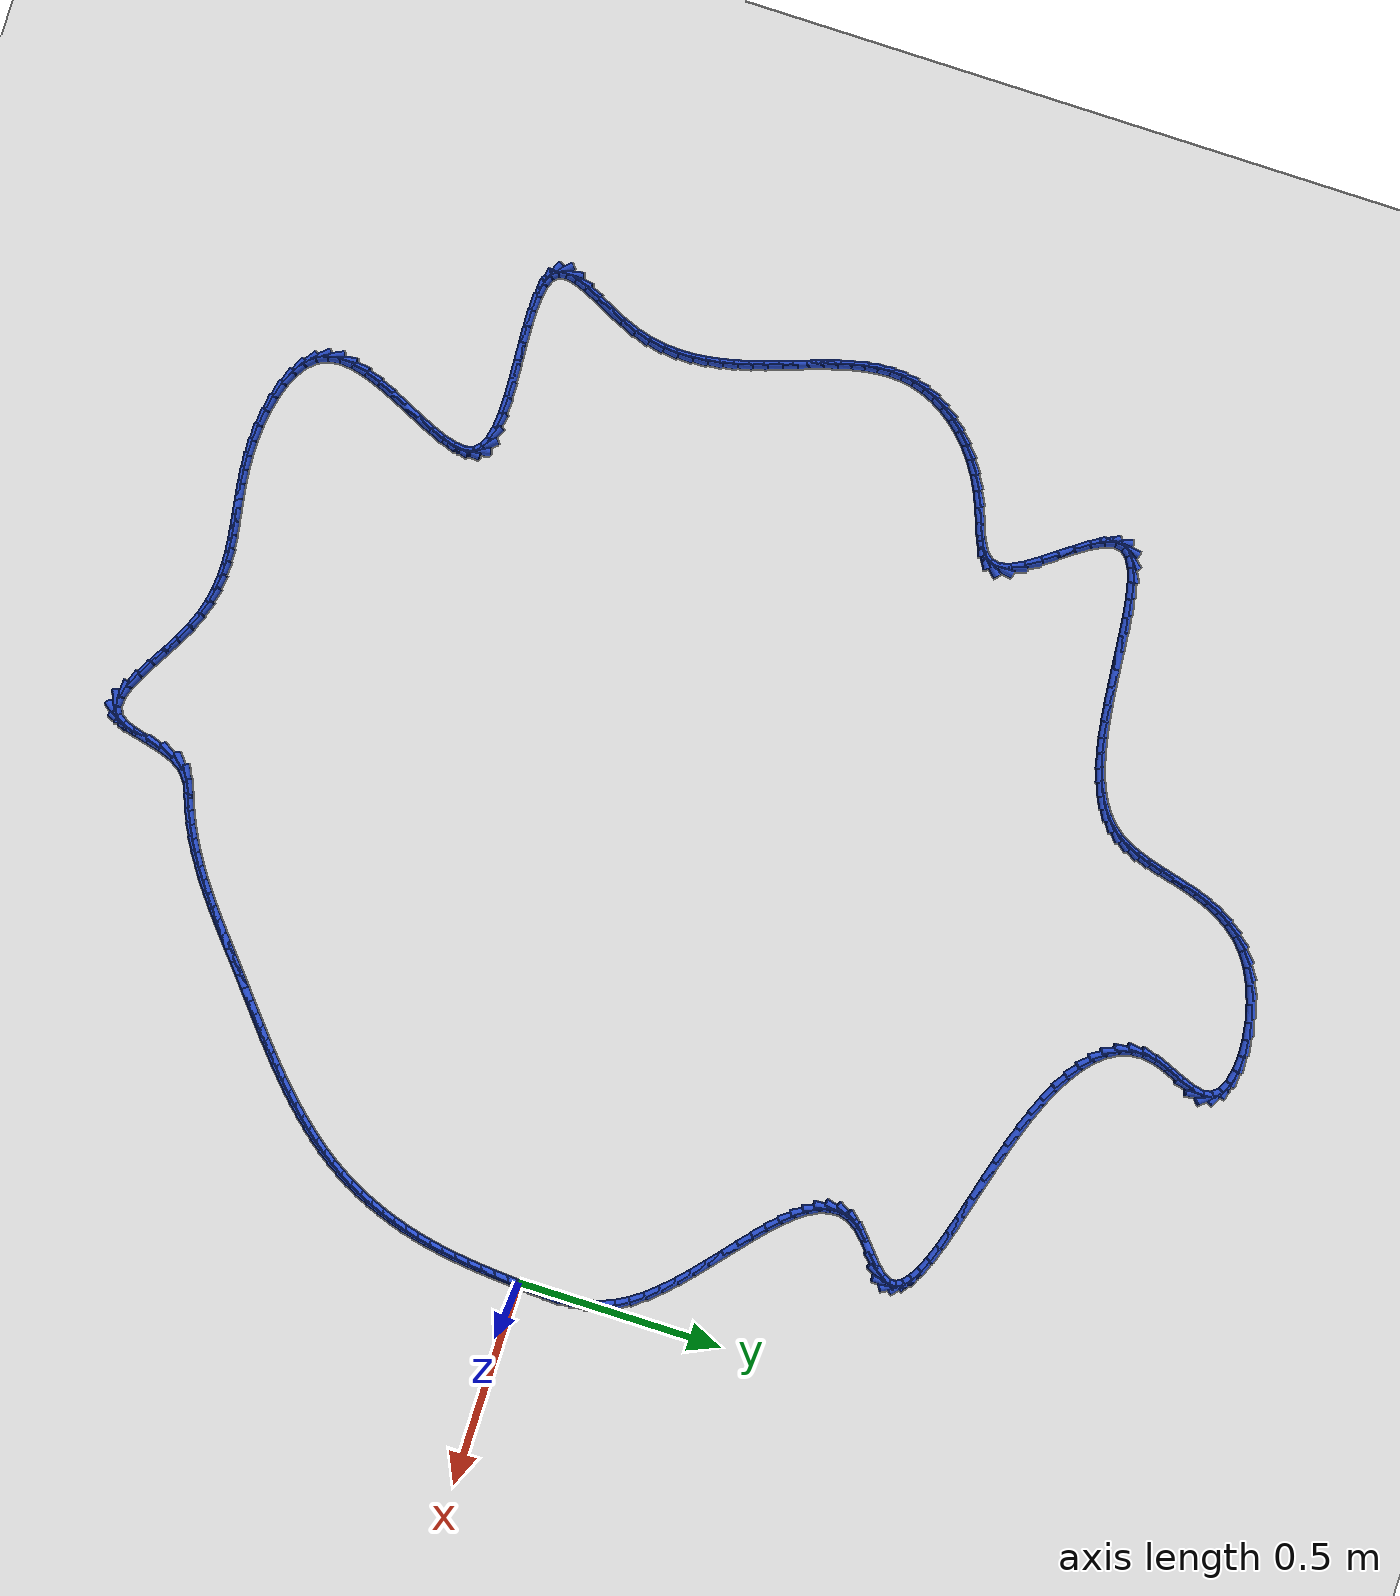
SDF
<sdf version="1.6">
 <world name="default">
  <light name="sun" type="directional">
   <pose>0 0 10 0 -0 0</pose>
   <diffuse>0.8 0.8 0.8 1</diffuse>
   <specular>0.2 0.2 0.2 1</specular>
   <attenuation>
    <range>1000</range>
    <constant>0.9</constant>
    <linear>0.01</linear>
    <quadratic>0.001</quadratic>
   </attenuation>
   <direction>-0.5 0.1 -0.9</direction>
  </light>
  <model name="ground_plane">
   <static>1</static>
   <link name="link">
    <collision name="collision">
     <geometry><plane><normal>0 0 1</normal><size>100 100</size></plane></geometry>
     <surface><friction><ode><mu>100</mu><mu2>50</mu2></ode></friction></surface>
    </collision>
    <visual name="visual">
     <cast_shadows>0</cast_shadows>
     <geometry><plane><normal>0 0 1</normal><size>100 100</size></plane></geometry>
     <material>
      <script><uri>file://media/materials/scripts/gazebo.material</uri><name>Gazebo/WhiteGlow</name></script>
     </material>
    </visual>
   </link>
  </model>
  <gravity>0 0 -9.8</gravity>
  <magnetic_field>6e-06 2.3e-05 -4.2e-05</magnetic_field>
  <atmosphere type="adiabatic"/>
  <physics name="default_physics" default="0" type="ode">
   <max_step_size>0.001</max_step_size>
   <real_time_factor>1</real_time_factor>
   <real_time_update_rate>1000</real_time_update_rate>
  </physics>
  <scene><ambient>0.4 0.4 0.4 1</ambient><background>0.7 0.7 0.7 1</background><shadows>1</shadows></scene>
  <spherical_coordinates>
   <surface_model>EARTH_WGS84</surface_model>
   <latitude_deg>0</latitude_deg>
   <longitude_deg>0</longitude_deg>
   <elevation>0</elevation>
   <heading_deg>0</heading_deg>
  </spherical_coordinates>
  <model name="line">
   <link name="link_0">
    <pose>1.734723475976807e-18 -6.245004513516506e-17 0.01 0 1.57 1.5070492738437389</pose>
    <collision name="collision">
     <geometry><cylinder><radius>0.01</radius><length>0.08</length></cylinder></geometry>
    </collision>
    <visual name="visual">
     <material>
      <script><name>Gazebo/Blue</name><uri>file://media/materials/scripts/gazebo.material</uri></script>
     </material>
     <geometry><cylinder><radius>0.01</radius><length>0.08</length></cylinder></geometry>
    </visual>
   </link>
   <link name="link_1">
    <pose>0.002135402018232102 0.03345266330930316 0.01 0 1.57 1.5297991189124072</pose>
    <collision name="collision">
     <geometry><cylinder><radius>0.01</radius><length>0.08</length></cylinder></geometry>
    </collision>
    <visual name="visual">
     <material>
      <script><name>Gazebo/Blue</name><uri>file://media/materials/scripts/gazebo.material</uri></script>
     </material>
     <geometry><cylinder><radius>0.01</radius><length>0.08</length></cylinder></geometry>
    </visual>
   </link>
   <link name="link_2">
    <pose>0.0035087740667446364 0.06693305360533194 0.01 0 1.57 -1.5687584165227297</pose>
    <collision name="collision">
     <geometry><cylinder><radius>0.01</radius><length>0.08</length></cylinder></geometry>
    </collision>
    <visual name="visual">
     <material>
      <script><name>Gazebo/Blue</name><uri>file://media/materials/scripts/gazebo.material</uri></script>
     </material>
     <geometry><cylinder><radius>0.01</radius><length>0.08</length></cylinder></geometry>
    </visual>
   </link>
   <link name="link_3">
    <pose>0.0034407187152398306 0.10032768251573597 0.01 0 1.57 -1.5049523425660776</pose>
    <collision name="collision">
     <geometry><cylinder><radius>0.01</radius><length>0.08</length></cylinder></geometry>
    </collision>
    <visual name="visual">
     <material>
      <script><name>Gazebo/Blue</name><uri>file://media/materials/scripts/gazebo.material</uri></script>
     </material>
     <geometry><cylinder><radius>0.01</radius><length>0.08</length></cylinder></geometry>
    </visual>
   </link>
   <link name="link_4">
    <pose>0.0012518385334199114 0.1335230616681649 0.01 0 1.57 -1.4202202495845495</pose>
    <collision name="collision">
     <geometry><cylinder><radius>0.01</radius><length>0.08</length></cylinder></geometry>
    </collision>
    <visual name="visual">
     <material>
      <script><name>Gazebo/Blue</name><uri>file://media/materials/scripts/gazebo.material</uri></script>
     </material>
     <geometry><cylinder><radius>0.01</radius><length>0.08</length></cylinder></geometry>
    </visual>
   </link>
   <link name="link_5">
    <pose>-0.003737263909012894 0.16640570269026855 0.01 0 1.57 -1.3155611060862418</pose>
    <collision name="collision">
     <geometry><cylinder><radius>0.01</radius><length>0.08</length></cylinder></geometry>
    </collision>
    <visual name="visual">
     <material>
      <script><name>Gazebo/Blue</name><uri>file://media/materials/scripts/gazebo.material</uri></script>
     </material>
     <geometry><cylinder><radius>0.01</radius><length>0.08</length></cylinder></geometry>
    </visual>
   </link>
   <link name="link_6">
    <pose>-0.012205986042356357 0.19886211720969643 0.01 0 1.57 -1.1940483547402347</pose>
    <collision name="collision">
     <geometry><cylinder><radius>0.01</radius><length>0.08</length></cylinder></geometry>
    </collision>
    <visual name="visual">
     <material>
      <script><name>Gazebo/Blue</name><uri>file://media/materials/scripts/gazebo.material</uri></script>
     </material>
     <geometry><cylinder><radius>0.01</radius><length>0.08</length></cylinder></geometry>
    </visual>
   </link>
   <link name="link_7">
    <pose>-0.024833725296908263 0.23077881685409832 0.01 0 1.57 -1.0637630969239575</pose>
    <collision name="collision">
     <geometry><cylinder><radius>0.01</radius><length>0.08</length></cylinder></geometry>
    </collision>
    <visual name="visual">
     <material>
      <script><name>Gazebo/Blue</name><uri>file://media/materials/scripts/gazebo.material</uri></script>
     </material>
     <geometry><cylinder><radius>0.01</radius><length>0.08</length></cylinder></geometry>
    </visual>
   </link>
   <link name="link_8">
    <pose>-0.04220484899709303 0.26205164778055207 0.01 0 1.57 -0.9517172667167824</pose>
    <collision name="collision">
     <geometry><cylinder><radius>0.01</radius><length>0.08</length></cylinder></geometry>
    </collision>
    <visual name="visual">
     <material>
      <script><name>Gazebo/Blue</name><uri>file://media/materials/scripts/gazebo.material</uri></script>
     </material>
     <geometry><cylinder><radius>0.01</radius><length>0.08</length></cylinder></geometry>
    </visual>
   </link>
   <link name="link_9">
    <pose>-0.0640164712059616 0.2926636084396363 0.01 0 1.57 -0.8666658943532133</pose>
    <collision name="collision">
     <geometry><cylinder><radius>0.01</radius><length>0.08</length></cylinder></geometry>
    </collision>
    <visual name="visual">
     <material>
      <script><name>Gazebo/Blue</name><uri>file://media/materials/scripts/gazebo.material</uri></script>
     </material>
     <geometry><cylinder><radius>0.01</radius><length>0.08</length></cylinder></geometry>
    </visual>
   </link>
   <link name="link_10">
    <pose>-0.08948205486747239 0.3226452049171433 0.01 0 1.57 -0.8036611257417363</pose>
    <collision name="collision">
     <geometry><cylinder><radius>0.01</radius><length>0.08</length></cylinder></geometry>
    </collision>
    <visual name="visual">
     <material>
      <script><name>Gazebo/Blue</name><uri>file://media/materials/scripts/gazebo.material</uri></script>
     </material>
     <geometry><cylinder><radius>0.01</radius><length>0.08</length></cylinder></geometry>
    </visual>
   </link>
   <link name="link_11">
    <pose>-0.11781019244035959 0.3520274217123871 0.01 0 1.57 -0.7586290285794716</pose>
    <collision name="collision">
     <geometry><cylinder><radius>0.01</radius><length>0.08</length></cylinder></geometry>
    </collision>
    <visual name="visual">
     <material>
      <script><name>Gazebo/Blue</name><uri>file://media/materials/scripts/gazebo.material</uri></script>
     </material>
     <geometry><cylinder><radius>0.01</radius><length>0.08</length></cylinder></geometry>
    </visual>
   </link>
   <link name="link_12">
    <pose>-0.14820947638335744 0.38084124332468205 0.01 0 1.57 -0.7287066243767716</pose>
    <collision name="collision">
     <geometry><cylinder><radius>0.01</radius><length>0.08</length></cylinder></geometry>
    </collision>
    <visual name="visual">
     <material>
      <script><name>Gazebo/Blue</name><uri>file://media/materials/scripts/gazebo.material</uri></script>
     </material>
     <geometry><cylinder><radius>0.01</radius><length>0.08</length></cylinder></geometry>
    </visual>
   </link>
   <link name="link_13">
    <pose>-0.1798884991552002 0.4091176542533424 0.01 0 1.57 -0.7121632643164727</pose>
    <collision name="collision">
     <geometry><cylinder><radius>0.01</radius><length>0.08</length></cylinder></geometry>
    </collision>
    <visual name="visual">
     <material>
      <script><name>Gazebo/Blue</name><uri>file://media/materials/scripts/gazebo.material</uri></script>
     </material>
     <geometry><cylinder><radius>0.01</radius><length>0.08</length></cylinder></geometry>
    </visual>
   </link>
   <link name="link_14">
    <pose>-0.21205585321462195 0.4368876389976821 0.01 0 1.57 -0.7083060552038007</pose>
    <collision name="collision">
     <geometry><cylinder><radius>0.01</radius><length>0.08</length></cylinder></geometry>
    </collision>
    <visual name="visual">
     <material>
      <script><name>Gazebo/Blue</name><uri>file://media/materials/scripts/gazebo.material</uri></script>
     </material>
     <geometry><cylinder><radius>0.01</radius><length>0.08</length></cylinder></geometry>
    </visual>
   </link>
   <link name="link_15">
    <pose>-0.24392013102035703 0.4641821820570155 0.01 0 1.57 -0.717475798740363</pose>
    <collision name="collision">
     <geometry><cylinder><radius>0.01</radius><length>0.08</length></cylinder></geometry>
    </collision>
    <visual name="visual">
     <material>
      <script><name>Gazebo/Blue</name><uri>file://media/materials/scripts/gazebo.material</uri></script>
     </material>
     <geometry><cylinder><radius>0.01</radius><length>0.08</length></cylinder></geometry>
    </visual>
   </link>
   <link name="link_16">
    <pose>-0.2746899250311396 0.49103226793065685 0.01 0 1.57 -0.7411886175281001</pose>
    <collision name="collision">
     <geometry><cylinder><radius>0.01</radius><length>0.08</length></cylinder></geometry>
    </collision>
    <visual name="visual">
     <material>
      <script><name>Gazebo/Blue</name><uri>file://media/materials/scripts/gazebo.material</uri></script>
     </material>
     <geometry><cylinder><radius>0.01</radius><length>0.08</length></cylinder></geometry>
    </visual>
   </link>
   <link name="link_17">
    <pose>-0.3035738277057039 0.5174688811179202 0.01 0 1.57 -0.7824805162899104</pose>
    <collision name="collision">
     <geometry><cylinder><radius>0.01</radius><length>0.08</length></cylinder></geometry>
    </collision>
    <visual name="visual">
     <material>
      <script><name>Gazebo/Blue</name><uri>file://media/materials/scripts/gazebo.material</uri></script>
     </material>
     <geometry><cylinder><radius>0.01</radius><length>0.08</length></cylinder></geometry>
    </visual>
   </link>
   <link name="link_18">
    <pose>-0.3297804315027842 0.5435230061181201 0.01 0 1.57 -0.8465253045443074</pose>
    <collision name="collision">
     <geometry><cylinder><radius>0.01</radius><length>0.08</length></cylinder></geometry>
    </collision>
    <visual name="visual">
     <material>
      <script><name>Gazebo/Blue</name><uri>file://media/materials/scripts/gazebo.material</uri></script>
     </material>
     <geometry><cylinder><radius>0.01</radius><length>0.08</length></cylinder></geometry>
    </visual>
   </link>
   <link name="link_19">
    <pose>-0.35251832888111456 0.5692256274305701 0.01 0 1.57 -0.9415344928984355</pose>
    <collision name="collision">
     <geometry><cylinder><radius>0.01</radius><length>0.08</length></cylinder></geometry>
    </collision>
    <visual name="visual">
     <material>
      <script><name>Gazebo/Blue</name><uri>file://media/materials/scripts/gazebo.material</uri></script>
     </material>
     <geometry><cylinder><radius>0.01</radius><length>0.08</length></cylinder></geometry>
    </visual>
   </link>
   <link name="link_20">
    <pose>-0.3709961122994293 0.5946077295545851 0.01 0 1.57 -1.0794884615568994</pose>
    <collision name="collision">
     <geometry><cylinder><radius>0.01</radius><length>0.08</length></cylinder></geometry>
    </collision>
    <visual name="visual">
     <material>
      <script><name>Gazebo/Blue</name><uri>file://media/materials/scripts/gazebo.material</uri></script>
     </material>
     <geometry><cylinder><radius>0.01</radius><length>0.08</length></cylinder></geometry>
    </visual>
   </link>
   <link name="link_21">
    <pose>-0.38442237421646264 0.6197002969894788 0.01 0 1.57 -1.2744287445054</pose>
    <collision name="collision">
     <geometry><cylinder><radius>0.01</radius><length>0.08</length></cylinder></geometry>
    </collision>
    <visual name="visual">
     <material>
      <script><name>Gazebo/Blue</name><uri>file://media/materials/scripts/gazebo.material</uri></script>
     </material>
     <geometry><cylinder><radius>0.01</radius><length>0.08</length></cylinder></geometry>
    </visual>
   </link>
   <link name="link_22">
    <pose>-0.3920057070909488 0.6445343142345655 0.01 0 1.57 -1.5322484609181006</pose>
    <collision name="collision">
     <geometry><cylinder><radius>0.01</radius><length>0.08</length></cylinder></geometry>
    </collision>
    <visual name="visual">
     <material>
      <script><name>Gazebo/Blue</name><uri>file://media/materials/scripts/gazebo.material</uri></script>
     </material>
     <geometry><cylinder><radius>0.01</radius><length>0.08</length></cylinder></geometry>
    </visual>
   </link>
   <link name="link_23">
    <pose>-0.392954703381622 0.6691407657891597 0.01 0 1.57 1.3114393307876295</pose>
    <collision name="collision">
     <geometry><cylinder><radius>0.01</radius><length>0.08</length></cylinder></geometry>
    </collision>
    <visual name="visual">
     <material>
      <script><name>Gazebo/Blue</name><uri>file://media/materials/scripts/gazebo.material</uri></script>
     </material>
     <geometry><cylinder><radius>0.01</radius><length>0.08</length></cylinder></geometry>
    </visual>
   </link>
   <link name="link_24">
    <pose>-0.3864779555472164 0.6935506361525754 0.01 0 1.57 1.025920335630295</pose>
    <collision name="collision">
     <geometry><cylinder><radius>0.01</radius><length>0.08</length></cylinder></geometry>
    </collision>
    <visual name="visual">
     <material>
      <script><name>Gazebo/Blue</name><uri>file://media/materials/scripts/gazebo.material</uri></script>
     </material>
     <geometry><cylinder><radius>0.01</radius><length>0.08</length></cylinder></geometry>
    </visual>
   </link>
   <link name="link_25">
    <pose>-0.3717840560464664 0.7177949098241267 0.01 0 1.57 0.8119694466412167</pose>
    <collision name="collision">
     <geometry><cylinder><radius>0.01</radius><length>0.08</length></cylinder></geometry>
    </collision>
    <visual name="visual">
     <material>
      <script><name>Gazebo/Blue</name><uri>file://media/materials/scripts/gazebo.material</uri></script>
     </material>
     <geometry><cylinder><radius>0.01</radius><length>0.08</length></cylinder></geometry>
    </visual>
   </link>
   <link name="link_26">
    <pose>-0.34899133599440757 0.7418322578082579 0.01 0 1.57 0.7193835196760918</pose>
    <collision name="collision">
     <geometry><cylinder><radius>0.01</radius><length>0.08</length></cylinder></geometry>
    </collision>
    <visual name="visual">
     <material>
      <script><name>Gazebo/Blue</name><uri>file://media/materials/scripts/gazebo.material</uri></script>
     </material>
     <geometry><cylinder><radius>0.01</radius><length>0.08</length></cylinder></geometry>
    </visual>
   </link>
   <link name="link_27">
    <pose>-0.32219502037355247 0.7653052349453995 0.01 0 1.57 0.7199081258582579</pose>
    <collision name="collision">
     <geometry><cylinder><radius>0.01</radius><length>0.08</length></cylinder></geometry>
    </collision>
    <visual name="visual">
     <material>
      <script><name>Gazebo/Blue</name><uri>file://media/materials/scripts/gazebo.material</uri></script>
     </material>
     <geometry><cylinder><radius>0.01</radius><length>0.08</length></cylinder></geometry>
    </visual>
   </link>
   <link name="link_28">
    <pose>-0.2965767435345856 0.7877700393429494 0.01 0 1.57 0.8288099615309701</pose>
    <collision name="collision">
     <geometry><cylinder><radius>0.01</radius><length>0.08</length></cylinder></geometry>
    </collision>
    <visual name="visual">
     <material>
      <script><name>Gazebo/Blue</name><uri>file://media/materials/scripts/gazebo.material</uri></script>
     </material>
     <geometry><cylinder><radius>0.01</radius><length>0.08</length></cylinder></geometry>
    </visual>
   </link>
   <link name="link_29">
    <pose>-0.2773129616532416 0.8087834247080015 0.01 0 1.57 1.1197725075640763</pose>
    <collision name="collision">
     <geometry><cylinder><radius>0.01</radius><length>0.08</length></cylinder></geometry>
    </collision>
    <visual name="visual">
     <material>
      <script><name>Gazebo/Blue</name><uri>file://media/materials/scripts/gazebo.material</uri></script>
     </material>
     <geometry><cylinder><radius>0.01</radius><length>0.08</length></cylinder></geometry>
    </visual>
   </link>
   <link name="link_30">
    <pose>-0.26796984127856066 0.8280747012228605 0.01 0 1.57 -1.5559711725776897</pose>
    <collision name="collision">
     <geometry><cylinder><radius>0.01</radius><length>0.08</length></cylinder></geometry>
    </collision>
    <visual name="visual">
     <material>
      <script><name>Gazebo/Blue</name><uri>file://media/materials/scripts/gazebo.material</uri></script>
     </material>
     <geometry><cylinder><radius>0.01</radius><length>0.08</length></cylinder></geometry>
    </visual>
   </link>
   <link name="link_31">
    <pose>-0.26823247875937084 0.8457890693436699 0.01 0 1.57 -1.0683605734121773</pose>
    <collision name="collision">
     <geometry><cylinder><radius>0.01</radius><length>0.08</length></cylinder></geometry>
    </collision>
    <visual name="visual">
     <material>
      <script><name>Gazebo/Blue</name><uri>file://media/materials/scripts/gazebo.material</uri></script>
     </material>
     <geometry><cylinder><radius>0.01</radius><length>0.08</length></cylinder></geometry>
    </visual>
   </link>
   <link name="link_32">
    <pose>-0.2772130369258734 0.8621331243134874 0.01 0 1.57 -0.7344808252903453</pose>
    <collision name="collision">
     <geometry><cylinder><radius>0.01</radius><length>0.08</length></cylinder></geometry>
    </collision>
    <visual name="visual">
     <material>
      <script><name>Gazebo/Blue</name><uri>file://media/materials/scripts/gazebo.material</uri></script>
     </material>
     <geometry><cylinder><radius>0.01</radius><length>0.08</length></cylinder></geometry>
    </visual>
   </link>
   <link name="link_33">
    <pose>-0.29402367860827 0.8773134613753719 0.01 0 1.57 -0.5395362167631712</pose>
    <collision name="collision">
     <geometry><cylinder><radius>0.01</radius><length>0.08</length></cylinder></geometry>
    </collision>
    <visual name="visual">
     <material>
      <script><name>Gazebo/Blue</name><uri>file://media/materials/scripts/gazebo.material</uri></script>
     </material>
     <geometry><cylinder><radius>0.01</radius><length>0.08</length></cylinder></geometry>
    </visual>
   </link>
   <link name="link_34">
    <pose>-0.3177765666367625 0.8915366757723823 0.01 0 1.57 -0.42450999438575854</pose>
    <collision name="collision">
     <geometry><cylinder><radius>0.01</radius><length>0.08</length></cylinder></geometry>
    </collision>
    <visual name="visual">
     <material>
      <script><name>Gazebo/Blue</name><uri>file://media/materials/scripts/gazebo.material</uri></script>
     </material>
     <geometry><cylinder><radius>0.01</radius><length>0.08</length></cylinder></geometry>
    </visual>
   </link>
   <link name="link_35">
    <pose>-0.34758386384155243 0.9050093627475775 0.01 0 1.57 -0.35408873358761106</pose>
    <collision name="collision">
     <geometry><cylinder><radius>0.01</radius><length>0.08</length></cylinder></geometry>
    </collision>
    <visual name="visual">
     <material>
      <script><name>Gazebo/Blue</name><uri>file://media/materials/scripts/gazebo.material</uri></script>
     </material>
     <geometry><cylinder><radius>0.01</radius><length>0.08</length></cylinder></geometry>
    </visual>
   </link>
   <link name="link_36">
    <pose>-0.382557733052841 0.9179381175440154 0.01 0 1.57 -0.3104095815001408</pose>
    <collision name="collision">
     <geometry><cylinder><radius>0.01</radius><length>0.08</length></cylinder></geometry>
    </collision>
    <visual name="visual">
     <material>
      <script><name>Gazebo/Blue</name><uri>file://media/materials/scripts/gazebo.material</uri></script>
     </material>
     <geometry><cylinder><radius>0.01</radius><length>0.08</length></cylinder></geometry>
    </visual>
   </link>
   <link name="link_37">
    <pose>-0.42181033710083005 0.9305295354047555 0.01 0 1.57 -0.28429085134923404</pose>
    <collision name="collision">
     <geometry><cylinder><radius>0.01</radius><length>0.08</length></cylinder></geometry>
    </collision>
    <visual name="visual">
     <material>
      <script><name>Gazebo/Blue</name><uri>file://media/materials/scripts/gazebo.material</uri></script>
     </material>
     <geometry><cylinder><radius>0.01</radius><length>0.08</length></cylinder></geometry>
    </visual>
   </link>
   <link name="link_38">
    <pose>-0.46445383881572166 0.9429902115728563 0.01 0 1.57 -0.2708608520059833</pose>
    <collision name="collision">
     <geometry><cylinder><radius>0.01</radius><length>0.08</length></cylinder></geometry>
    </collision>
    <visual name="visual">
     <material>
      <script><name>Gazebo/Blue</name><uri>file://media/materials/scripts/gazebo.material</uri></script>
     </material>
     <geometry><cylinder><radius>0.01</radius><length>0.08</length></cylinder></geometry>
    </visual>
   </link>
   <link name="link_39">
    <pose>-0.5096004010277171 0.9555267412913764 0.01 0 1.57 -0.26756058522104575</pose>
    <collision name="collision">
     <geometry><cylinder><radius>0.01</radius><length>0.08</length></cylinder></geometry>
    </collision>
    <visual name="visual">
     <material>
      <script><name>Gazebo/Blue</name><uri>file://media/materials/scripts/gazebo.material</uri></script>
     </material>
     <geometry><cylinder><radius>0.01</radius><length>0.08</length></cylinder></geometry>
    </visual>
   </link>
   <link name="link_40">
    <pose>-0.5563621865670174 0.9683457198033746 0.01 0 1.57 -0.2732245457701548</pose>
    <collision name="collision">
     <geometry><cylinder><radius>0.01</radius><length>0.08</length></cylinder></geometry>
    </collision>
    <visual name="visual">
     <material>
      <script><name>Gazebo/Blue</name><uri>file://media/materials/scripts/gazebo.material</uri></script>
     </material>
     <geometry><cylinder><radius>0.01</radius><length>0.08</length></cylinder></geometry>
    </visual>
   </link>
   <link name="link_41">
    <pose>-0.6038513582638247 0.9816537423519094 0.01 0 1.57 -0.28767348124354297</pose>
    <collision name="collision">
     <geometry><cylinder><radius>0.01</radius><length>0.08</length></cylinder></geometry>
    </collision>
    <visual name="visual">
     <material>
      <script><name>Gazebo/Blue</name><uri>file://media/materials/scripts/gazebo.material</uri></script>
     </material>
     <geometry><cylinder><radius>0.01</radius><length>0.08</length></cylinder></geometry>
    </visual>
   </link>
   <link name="link_42">
    <pose>-0.6511800789483412 0.9956574041800399 0.01 0 1.57 -0.3115865338625908</pose>
    <collision name="collision">
     <geometry><cylinder><radius>0.01</radius><length>0.08</length></cylinder></geometry>
    </collision>
    <visual name="visual">
     <material>
      <script><name>Gazebo/Blue</name><uri>file://media/materials/scripts/gazebo.material</uri></script>
     </material>
     <geometry><cylinder><radius>0.01</radius><length>0.08</length></cylinder></geometry>
    </visual>
   </link>
   <link name="link_43">
    <pose>-0.6974605114507677 1.0105633005308245 0.01 0 1.57 -0.34630769540061374</pose>
    <collision name="collision">
     <geometry><cylinder><radius>0.01</radius><length>0.08</length></cylinder></geometry>
    </collision>
    <visual name="visual">
     <material>
      <script><name>Gazebo/Blue</name><uri>file://media/materials/scripts/gazebo.material</uri></script>
     </material>
     <geometry><cylinder><radius>0.01</radius><length>0.08</length></cylinder></geometry>
    </visual>
   </link>
   <link name="link_44">
    <pose>-0.7418235955837313 1.0265717114174886 0.01 0 1.57 -0.39124432322262953</pose>
    <collision name="collision">
     <geometry><cylinder><radius>0.01</radius><length>0.08</length></cylinder></geometry>
    </collision>
    <visual name="visual">
     <material>
      <script><name>Gazebo/Blue</name><uri>file://media/materials/scripts/gazebo.material</uri></script>
     </material>
     <geometry><cylinder><radius>0.01</radius><length>0.08</length></cylinder></geometry>
    </visual>
   </link>
   <link name="link_45">
    <pose>-0.7836144713511344 1.0438108752755682 0.01 0 1.57 -0.44702168474161225</pose>
    <collision name="collision">
     <geometry><cylinder><radius>0.01</radius><length>0.08</length></cylinder></geometry>
    </collision>
    <visual name="visual">
     <material>
      <script><name>Gazebo/Blue</name><uri>file://media/materials/scripts/gazebo.material</uri></script>
     </material>
     <geometry><cylinder><radius>0.01</radius><length>0.08</length></cylinder></geometry>
    </visual>
   </link>
   <link name="link_46">
    <pose>-0.8223145584044129 1.0623631958438264 0.01 0 1.57 -0.5168673470197425</pose>
    <collision name="collision">
     <geometry><cylinder><radius>0.01</radius><length>0.08</length></cylinder></geometry>
    </collision>
    <visual name="visual">
     <material>
      <script><name>Gazebo/Blue</name><uri>file://media/materials/scripts/gazebo.material</uri></script>
     </material>
     <geometry><cylinder><radius>0.01</radius><length>0.08</length></cylinder></geometry>
    </visual>
   </link>
   <link name="link_47">
    <pose>-0.8574074632578579 1.0823103413572492 0.01 0 1.57 -0.6051807832206538</pose>
    <collision name="collision">
     <geometry><cylinder><radius>0.01</radius><length>0.08</length></cylinder></geometry>
    </collision>
    <visual name="visual">
     <material>
      <script><name>Gazebo/Blue</name><uri>file://media/materials/scripts/gazebo.material</uri></script>
     </material>
     <geometry><cylinder><radius>0.01</radius><length>0.08</length></cylinder></geometry>
    </visual>
   </link>
   <link name="link_48">
    <pose>-0.8883767924257594 1.1037339800508204 0.01 0 1.57 -0.717615706751163</pose>
    <collision name="collision">
     <geometry><cylinder><radius>0.01</radius><length>0.08</length></cylinder></geometry>
    </collision>
    <visual name="visual">
     <material>
      <script><name>Gazebo/Blue</name><uri>file://media/materials/scripts/gazebo.material</uri></script>
     </material>
     <geometry><cylinder><radius>0.01</radius><length>0.08</length></cylinder></geometry>
    </visual>
   </link>
   <link name="link_49">
    <pose>-0.9147061524224076 1.1267157801595244 0.01 0 1.57 -0.8605627752418685</pose>
    <collision name="collision">
     <geometry><cylinder><radius>0.01</radius><length>0.08</length></cylinder></geometry>
    </collision>
    <visual name="visual">
     <material>
      <script><name>Gazebo/Blue</name><uri>file://media/materials/scripts/gazebo.material</uri></script>
     </material>
     <geometry><cylinder><radius>0.01</radius><length>0.08</length></cylinder></geometry>
    </visual>
   </link>
   <link name="link_50">
    <pose>-0.9358791497620937 1.1513374099183473 0.01 0 1.57 -1.0389514572612926</pose>
    <collision name="collision">
     <geometry><cylinder><radius>0.01</radius><length>0.08</length></cylinder></geometry>
    </collision>
    <visual name="visual">
     <material>
      <script><name>Gazebo/Blue</name><uri>file://media/materials/scripts/gazebo.material</uri></script>
     </material>
     <geometry><cylinder><radius>0.01</radius><length>0.08</length></cylinder></geometry>
    </visual>
   </link>
   <link name="link_51">
    <pose>-0.9513793909591076 1.177680537562273 0.01 0 1.57 -1.2513179724322299</pose>
    <collision name="collision">
     <geometry><cylinder><radius>0.01</radius><length>0.08</length></cylinder></geometry>
    </collision>
    <visual name="visual">
     <material>
      <script><name>Gazebo/Blue</name><uri>file://media/materials/scripts/gazebo.material</uri></script>
     </material>
     <geometry><cylinder><radius>0.01</radius><length>0.08</length></cylinder></geometry>
    </visual>
   </link>
   <link name="link_52">
    <pose>-0.9606904825277395 1.205826831326286 0.01 0 1.57 -1.4842514592352918</pose>
    <collision name="collision">
     <geometry><cylinder><radius>0.01</radius><length>0.08</length></cylinder></geometry>
    </collision>
    <visual name="visual">
     <material>
      <script><name>Gazebo/Blue</name><uri>file://media/materials/scripts/gazebo.material</uri></script>
     </material>
     <geometry><cylinder><radius>0.01</radius><length>0.08</length></cylinder></geometry>
    </visual>
   </link>
   <link name="link_53">
    <pose>-0.9632960309822802 1.2358579594453716 0.01 0 1.57 1.4275258089232647</pose>
    <collision name="collision">
     <geometry><cylinder><radius>0.01</radius><length>0.08</length></cylinder></geometry>
    </collision>
    <visual name="visual">
     <material>
      <script><name>Gazebo/Blue</name><uri>file://media/materials/scripts/gazebo.material</uri></script>
     </material>
     <geometry><cylinder><radius>0.01</radius><length>0.08</length></cylinder></geometry>
    </visual>
   </link>
   <link name="link_54">
    <pose>-0.958680112505247 1.2678554174600565 0.01 0 1.57 1.2471528208891973</pose>
    <collision name="collision">
     <geometry><cylinder><radius>0.01</radius><length>0.08</length></cylinder></geometry>
    </collision>
    <visual name="visual">
     <material>
      <script><name>Gazebo/Blue</name><uri>file://media/materials/scripts/gazebo.material</uri></script>
     </material>
     <geometry><cylinder><radius>0.01</radius><length>0.08</length></cylinder></geometry>
    </visual>
   </link>
   <link name="link_55">
    <pose>-0.9473913300000234 1.3015092802131996 0.01 0 1.57 1.175788893862983</pose>
    <collision name="collision">
     <geometry><cylinder><radius>0.01</radius><length>0.08</length></cylinder></geometry>
    </collision>
    <visual name="visual">
     <material>
      <script><name>Gazebo/Blue</name><uri>file://media/materials/scripts/gazebo.material</uri></script>
     </material>
     <geometry><cylinder><radius>0.01</radius><length>0.08</length></cylinder></geometry>
    </visual>
   </link>
   <link name="link_56">
    <pose>-0.9333096664231255 1.335284692182798 0.01 0 1.57 1.2039046054131186</pose>
    <collision name="collision">
     <geometry><cylinder><radius>0.01</radius><length>0.08</length></cylinder></geometry>
    </collision>
    <visual name="visual">
     <material>
      <script><name>Gazebo/Blue</name><uri>file://media/materials/scripts/gazebo.material</uri></script>
     </material>
     <geometry><cylinder><radius>0.01</radius><length>0.08</length></cylinder></geometry>
    </visual>
   </link>
   <link name="link_57">
    <pose>-0.920965015523969 1.3674078291756169 0.01 0 1.57 1.3620903950497678</pose>
    <collision name="collision">
     <geometry><cylinder><radius>0.01</radius><length>0.08</length></cylinder></geometry>
    </collision>
    <visual name="visual">
     <material>
      <script><name>Gazebo/Blue</name><uri>file://media/materials/scripts/gazebo.material</uri></script>
     </material>
     <geometry><cylinder><radius>0.01</radius><length>0.08</length></cylinder></geometry>
    </visual>
   </link>
   <link name="link_58">
    <pose>-0.9148872710519703 1.39610486699842 0.01 0 1.57 -1.3867115211086347</pose>
    <collision name="collision">
     <geometry><cylinder><radius>0.01</radius><length>0.08</length></cylinder></geometry>
    </collision>
    <visual name="visual">
     <material>
      <script><name>Gazebo/Blue</name><uri>file://media/materials/scripts/gazebo.material</uri></script>
     </material>
     <geometry><cylinder><radius>0.01</radius><length>0.08</length></cylinder></geometry>
    </visual>
   </link>
   <link name="link_59">
    <pose>-0.9192813065985592 1.4197042572916903 0.01 0 1.57 -0.8629041615421474</pose>
    <collision name="collision">
     <geometry><cylinder><radius>0.01</radius><length>0.08</length></cylinder></geometry>
    </collision>
    <visual name="visual">
     <material>
      <script><name>Gazebo/Blue</name><uri>file://media/materials/scripts/gazebo.material</uri></script>
     </material>
     <geometry><cylinder><radius>0.01</radius><length>0.08</length></cylinder></geometry>
    </visual>
   </link>
   <link name="link_60">
    <pose>-0.9346758364334732 1.4376912484369107 0.01 0 1.57 -0.47307711145588516</pose>
    <collision name="collision">
     <geometry><cylinder><radius>0.01</radius><length>0.08</length></cylinder></geometry>
    </collision>
    <visual name="visual">
     <material>
      <script><name>Gazebo/Blue</name><uri>file://media/materials/scripts/gazebo.material</uri></script>
     </material>
     <geometry><cylinder><radius>0.01</radius><length>0.08</length></cylinder></geometry>
    </visual>
   </link>
   <link name="link_61">
    <pose>-0.9592755026900848 1.450282417041009 0.01 0 1.57 -0.2281382153872773</pose>
    <collision name="collision">
     <geometry><cylinder><radius>0.01</radius><length>0.08</length></cylinder></geometry>
    </collision>
    <visual name="visual">
     <material>
      <script><name>Gazebo/Blue</name><uri>file://media/materials/scripts/gazebo.material</uri></script>
     </material>
     <geometry><cylinder><radius>0.01</radius><length>0.08</length></cylinder></geometry>
    </visual>
   </link>
   <link name="link_62">
    <pose>-0.9912482983002132 1.4577058723114358 0.01 0 1.57 -0.06611495418680223</pose>
    <collision name="collision">
     <geometry><cylinder><radius>0.01</radius><length>0.08</length></cylinder></geometry>
    </collision>
    <visual name="visual">
     <material>
      <script><name>Gazebo/Blue</name><uri>file://media/materials/scripts/gazebo.material</uri></script>
     </material>
     <geometry><cylinder><radius>0.01</radius><length>0.08</length></cylinder></geometry>
    </visual>
   </link>
   <link name="link_63">
    <pose>-1.0287622161956773 1.4601897234556418 0.01 0 1.57 0.05398630363658327</pose>
    <collision name="collision">
     <geometry><cylinder><radius>0.01</radius><length>0.08</length></cylinder></geometry>
    </collision>
    <visual name="visual">
     <material>
      <script><name>Gazebo/Blue</name><uri>file://media/materials/scripts/gazebo.material</uri></script>
     </material>
     <geometry><cylinder><radius>0.01</radius><length>0.08</length></cylinder></geometry>
    </visual>
   </link>
   <link name="link_64">
    <pose>-1.0699852493082962 1.4579620796810788 0.01 0 1.57 0.15446744971172885</pose>
    <collision name="collision">
     <geometry><cylinder><radius>0.01</radius><length>0.08</length></cylinder></geometry>
    </collision>
    <visual name="visual">
     <material>
      <script><name>Gazebo/Blue</name><uri>file://media/materials/scripts/gazebo.material</uri></script>
     </material>
     <geometry><cylinder><radius>0.01</radius><length>0.08</length></cylinder></geometry>
    </visual>
   </link>
   <link name="link_65">
    <pose>-1.113085390569889 1.4512510501951963 0.01 0 1.57 0.2489012379649305</pose>
    <collision name="collision">
     <geometry><cylinder><radius>0.01</radius><length>0.08</length></cylinder></geometry>
    </collision>
    <visual name="visual">
     <material>
      <script><name>Gazebo/Blue</name><uri>file://media/materials/scripts/gazebo.material</uri></script>
     </material>
     <geometry><cylinder><radius>0.01</radius><length>0.08</length></cylinder></geometry>
    </visual>
   </link>
   <link name="link_66">
    <pose>-1.1562306329122753 1.4402847442054467 0.01 0 1.57 0.3477899901577562</pose>
    <collision name="collision">
     <geometry><cylinder><radius>0.01</radius><length>0.08</length></cylinder></geometry>
    </collision>
    <visual name="visual">
     <material>
      <script><name>Gazebo/Blue</name><uri>file://media/materials/scripts/gazebo.material</uri></script>
     </material>
     <geometry><cylinder><radius>0.01</radius><length>0.08</length></cylinder></geometry>
    </visual>
   </link>
   <link name="link_67">
    <pose>-1.1975889692672745 1.42529127091928 0.01 0 1.57 0.46201020415396077</pose>
    <collision name="collision">
     <geometry><cylinder><radius>0.01</radius><length>0.08</length></cylinder></geometry>
    </collision>
    <visual name="visual">
     <material>
      <script><name>Gazebo/Blue</name><uri>file://media/materials/scripts/gazebo.material</uri></script>
     </material>
     <geometry><cylinder><radius>0.01</radius><length>0.08</length></cylinder></geometry>
    </visual>
   </link>
   <link name="link_68">
    <pose>-1.2353283925667047 1.4064987395441475 0.01 0 1.57 0.6037212552809045</pose>
    <collision name="collision">
     <geometry><cylinder><radius>0.01</radius><length>0.08</length></cylinder></geometry>
    </collision>
    <visual name="visual">
     <material>
      <script><name>Gazebo/Blue</name><uri>file://media/materials/scripts/gazebo.material</uri></script>
     </material>
     <geometry><cylinder><radius>0.01</radius><length>0.08</length></cylinder></geometry>
    </visual>
   </link>
   <link name="link_69">
    <pose>-1.2677364559943995 1.3841496937025077 0.01 0 1.57 0.7597947664931077</pose>
    <collision name="collision">
     <geometry><cylinder><radius>0.01</radius><length>0.08</length></cylinder></geometry>
    </collision>
    <visual name="visual">
     <material>
      <script><name>Gazebo/Blue</name><uri>file://media/materials/scripts/gazebo.material</uri></script>
     </material>
     <geometry><cylinder><radius>0.01</radius><length>0.08</length></cylinder></geometry>
    </visual>
   </link>
   <link name="link_70">
    <pose>-1.294562650023387 1.3586631755536782 0.01 0 1.57 0.9069400863230939</pose>
    <collision name="collision">
     <geometry><cylinder><radius>0.01</radius><length>0.08</length></cylinder></geometry>
    </collision>
    <visual name="visual">
     <material>
      <script><name>Gazebo/Blue</name><uri>file://media/materials/scripts/gazebo.material</uri></script>
     </material>
     <geometry><cylinder><radius>0.01</radius><length>0.08</length></cylinder></geometry>
    </visual>
   </link>
   <link name="link_71">
    <pose>-1.31653502925602 1.3305763685331644 0.01 0 1.57 1.0358592865323129</pose>
    <collision name="collision">
     <geometry><cylinder><radius>0.01</radius><length>0.08</length></cylinder></geometry>
    </collision>
    <visual name="visual">
     <material>
      <script><name>Gazebo/Blue</name><uri>file://media/materials/scripts/gazebo.material</uri></script>
     </material>
     <geometry><cylinder><radius>0.01</radius><length>0.08</length></cylinder></geometry>
    </visual>
   </link>
   <link name="link_72">
    <pose>-1.3343996234628712 1.3004286262043643 0.01 0 1.57 1.1413542212084051</pose>
    <collision name="collision">
     <geometry><cylinder><radius>0.01</radius><length>0.08</length></cylinder></geometry>
    </collision>
    <visual name="visual">
     <material>
      <script><name>Gazebo/Blue</name><uri>file://media/materials/scripts/gazebo.material</uri></script>
     </material>
     <geometry><cylinder><radius>0.01</radius><length>0.08</length></cylinder></geometry>
    </visual>
   </link>
   <link name="link_73">
    <pose>-1.348902462414513 1.2687593021306762 0.01 0 1.57 1.2216515014644793</pose>
    <collision name="collision">
     <geometry><cylinder><radius>0.01</radius><length>0.08</length></cylinder></geometry>
    </collision>
    <visual name="visual">
     <material>
      <script><name>Gazebo/Blue</name><uri>file://media/materials/scripts/gazebo.material</uri></script>
     </material>
     <geometry><cylinder><radius>0.01</radius><length>0.08</length></cylinder></geometry>
    </visual>
   </link>
   <link name="link_74">
    <pose>-1.3607895758815178 1.2361077498754989 0.01 0 1.57 1.2768716550753672</pose>
    <collision name="collision">
     <geometry><cylinder><radius>0.01</radius><length>0.08</length></cylinder></geometry>
    </collision>
    <visual name="visual">
     <material>
      <script><name>Gazebo/Blue</name><uri>file://media/materials/scripts/gazebo.material</uri></script>
     </material>
     <geometry><cylinder><radius>0.01</radius><length>0.08</length></cylinder></geometry>
    </visual>
   </link>
   <link name="link_75">
    <pose>-1.3708069936344573 1.2030133230022297 0.01 0 1.57 1.307527838596577</pose>
    <collision name="collision">
     <geometry><cylinder><radius>0.01</radius><length>0.08</length></cylinder></geometry>
    </collision>
    <visual name="visual">
     <material>
      <script><name>Gazebo/Blue</name><uri>file://media/materials/scripts/gazebo.material</uri></script>
     </material>
     <geometry><cylinder><radius>0.01</radius><length>0.08</length></cylinder></geometry>
    </visual>
   </link>
   <link name="link_76">
    <pose>-1.3797007454439048 1.1700153750742688 0.01 0 1.57 1.3134792738217023</pose>
    <collision name="collision">
     <geometry><cylinder><radius>0.01</radius><length>0.08</length></cylinder></geometry>
    </collision>
    <visual name="visual">
     <material>
      <script><name>Gazebo/Blue</name><uri>file://media/materials/scripts/gazebo.material</uri></script>
     </material>
     <geometry><cylinder><radius>0.01</radius><length>0.08</length></cylinder></geometry>
    </visual>
   </link>
   <link name="link_77">
    <pose>-1.3882168610804313 1.1376532596550133 0.01 0 1.57 1.2932688464191024</pose>
    <collision name="collision">
     <geometry><cylinder><radius>0.01</radius><length>0.08</length></cylinder></geometry>
    </collision>
    <visual name="visual">
     <material>
      <script><name>Gazebo/Blue</name><uri>file://media/materials/scripts/gazebo.material</uri></script>
     </material>
     <geometry><cylinder><radius>0.01</radius><length>0.08</length></cylinder></geometry>
    </visual>
   </link>
   <link name="link_78">
    <pose>-1.3971013703146107 1.1064663303078615 0.01 0 1.57 1.2437173441911602</pose>
    <collision name="collision">
     <geometry><cylinder><radius>0.01</radius><length>0.08</length></cylinder></geometry>
    </collision>
    <visual name="visual">
     <material>
      <script><name>Gazebo/Blue</name><uri>file://media/materials/scripts/gazebo.material</uri></script>
     </material>
     <geometry><cylinder><radius>0.01</radius><length>0.08</length></cylinder></geometry>
    </visual>
   </link>
   <link name="link_79">
    <pose>-1.4071003029170144 1.0769939405962132 0.01 0 1.57 1.159888846898884</pose>
    <collision name="collision">
     <geometry><cylinder><radius>0.01</radius><length>0.08</length></cylinder></geometry>
    </collision>
    <visual name="visual">
     <material>
      <script><name>Gazebo/Blue</name><uri>file://media/materials/scripts/gazebo.material</uri></script>
     </material>
     <geometry><cylinder><radius>0.01</radius><length>0.08</length></cylinder></geometry>
    </visual>
   </link>
   <link name="link_80">
    <pose>-1.4189596886582148 1.0497754440834657 0.01 0 1.57 1.0364303493056322</pose>
    <collision name="collision">
     <geometry><cylinder><radius>0.01</radius><length>0.08</length></cylinder></geometry>
    </collision>
    <visual name="visual">
     <material>
      <script><name>Gazebo/Blue</name><uri>file://media/materials/scripts/gazebo.material</uri></script>
     </material>
     <geometry><cylinder><radius>0.01</radius><length>0.08</length></cylinder></geometry>
    </visual>
   </link>
   <link name="link_81">
    <pose>-1.4334182800691866 1.025343766039833 0.01 0 1.57 0.8872241552828292</pose>
    <collision name="collision">
     <geometry><cylinder><radius>0.01</radius><length>0.08</length></cylinder></geometry>
    </collision>
    <visual name="visual">
     <material>
      <script><name>Gazebo/Blue</name><uri>file://media/materials/scripts/gazebo.material</uri></script>
     </material>
     <geometry><cylinder><radius>0.01</radius><length>0.08</length></cylinder></geometry>
    </visual>
   </link>
   <link name="link_82">
    <pose>-1.450866455564414 1.0039240981603421 0.01 0 1.57 0.7414180585599348</pose>
    <collision name="collision">
     <geometry><cylinder><radius>0.01</radius><length>0.08</length></cylinder></geometry>
    </collision>
    <visual name="visual">
     <material>
      <script><name>Gazebo/Blue</name><uri>file://media/materials/scripts/gazebo.material</uri></script>
     </material>
     <geometry><cylinder><radius>0.01</radius><length>0.08</length></cylinder></geometry>
    </visual>
   </link>
   <link name="link_83">
    <pose>-1.4712000400719238 0.9853047721515661 0.01 0 1.57 0.6081002745427062</pose>
    <collision name="collision">
     <geometry><cylinder><radius>0.01</radius><length>0.08</length></cylinder></geometry>
    </collision>
    <visual name="visual">
     <material>
      <script><name>Gazebo/Blue</name><uri>file://media/materials/scripts/gazebo.material</uri></script>
     </material>
     <geometry><cylinder><radius>0.01</radius><length>0.08</length></cylinder></geometry>
    </visual>
   </link>
   <link name="link_84">
    <pose>-1.4942772156230748 0.9692408681591175 0.01 0 1.57 0.491713015799219</pose>
    <collision name="collision">
     <geometry><cylinder><radius>0.01</radius><length>0.08</length></cylinder></geometry>
    </collision>
    <visual name="visual">
     <material>
      <script><name>Gazebo/Blue</name><uri>file://media/materials/scripts/gazebo.material</uri></script>
     </material>
     <geometry><cylinder><radius>0.01</radius><length>0.08</length></cylinder></geometry>
    </visual>
   </link>
   <link name="link_85">
    <pose>-1.5199561642492265 0.9554874663286076 0.01 0 1.57 0.3936785784372846</pose>
    <collision name="collision">
     <geometry><cylinder><radius>0.01</radius><length>0.08</length></cylinder></geometry>
    </collision>
    <visual name="visual">
     <material>
      <script><name>Gazebo/Blue</name><uri>file://media/materials/scripts/gazebo.material</uri></script>
     </material>
     <geometry><cylinder><radius>0.01</radius><length>0.08</length></cylinder></geometry>
    </visual>
   </link>
   <link name="link_86">
    <pose>-1.5480950679817396 0.9437996468056485 0.01 0 1.57 0.313299706593923</pose>
    <collision name="collision">
     <geometry><cylinder><radius>0.01</radius><length>0.08</length></cylinder></geometry>
    </collision>
    <visual name="visual">
     <material>
      <script><name>Gazebo/Blue</name><uri>file://media/materials/scripts/gazebo.material</uri></script>
     </material>
     <geometry><cylinder><radius>0.01</radius><length>0.08</length></cylinder></geometry>
    </visual>
   </link>
   <link name="link_87">
    <pose>-1.5785521088519718 0.9339324897358522 0.01 0 1.57 0.2488129566157246</pose>
    <collision name="collision">
     <geometry><cylinder><radius>0.01</radius><length>0.08</length></cylinder></geometry>
    </collision>
    <visual name="visual">
     <material>
      <script><name>Gazebo/Blue</name><uri>file://media/materials/scripts/gazebo.material</uri></script>
     </material>
     <geometry><cylinder><radius>0.01</radius><length>0.08</length></cylinder></geometry>
    </visual>
   </link>
   <link name="link_88">
    <pose>-1.6111854688912837 0.9256410752648303 0.01 0 1.57 0.19814485238803176</pose>
    <collision name="collision">
     <geometry><cylinder><radius>0.01</radius><length>0.08</length></cylinder></geometry>
    </collision>
    <visual name="visual">
     <material>
      <script><name>Gazebo/Blue</name><uri>file://media/materials/scripts/gazebo.material</uri></script>
     </material>
     <geometry><cylinder><radius>0.01</radius><length>0.08</length></cylinder></geometry>
    </visual>
   </link>
   <link name="link_89">
    <pose>-1.645853330131034 0.9186804835381946 0.01 0 1.57 0.1593219658577773</pose>
    <collision name="collision">
     <geometry><cylinder><radius>0.01</radius><length>0.08</length></cylinder></geometry>
    </collision>
    <visual name="visual">
     <material>
      <script><name>Gazebo/Blue</name><uri>file://media/materials/scripts/gazebo.material</uri></script>
     </material>
     <geometry><cylinder><radius>0.01</radius><length>0.08</length></cylinder></geometry>
    </visual>
   </link>
   <link name="link_90">
    <pose>-1.6824138746025827 0.9128057947015573 0.01 0 1.57 0.13064088166499738</pose>
    <collision name="collision">
     <geometry><cylinder><radius>0.01</radius><length>0.08</length></cylinder></geometry>
    </collision>
    <visual name="visual">
     <material>
      <script><name>Gazebo/Blue</name><uri>file://media/materials/scripts/gazebo.material</uri></script>
     </material>
     <geometry><cylinder><radius>0.01</radius><length>0.08</length></cylinder></geometry>
    </visual>
   </link>
   <link name="link_91">
    <pose>-1.7207252843372898 0.9077720889005301 0.01 0 1.57 0.1107076073515535</pose>
    <collision name="collision">
     <geometry><cylinder><radius>0.01</radius><length>0.08</length></cylinder></geometry>
    </collision>
    <visual name="visual">
     <material>
      <script><name>Gazebo/Blue</name><uri>file://media/materials/scripts/gazebo.material</uri></script>
     </material>
     <geometry><cylinder><radius>0.01</radius><length>0.08</length></cylinder></geometry>
    </visual>
   </link>
   <link name="link_92">
    <pose>-1.7606457413665129 0.9033344462807247 0.01 0 1.57 0.09841808079191001</pose>
    <collision name="collision">
     <geometry><cylinder><radius>0.01</radius><length>0.08</length></cylinder></geometry>
    </collision>
    <visual name="visual">
     <material>
      <script><name>Gazebo/Blue</name><uri>file://media/materials/scripts/gazebo.material</uri></script>
     </material>
     <geometry><cylinder><radius>0.01</radius><length>0.08</length></cylinder></geometry>
    </visual>
   </link>
   <link name="link_93">
    <pose>-1.8020334277216128 0.8992479469877529 0.01 0 1.57 0.09291796974430584</pose>
    <collision name="collision">
     <geometry><cylinder><radius>0.01</radius><length>0.08</length></cylinder></geometry>
    </collision>
    <visual name="visual">
     <material>
      <script><name>Gazebo/Blue</name><uri>file://media/materials/scripts/gazebo.material</uri></script>
     </material>
     <geometry><cylinder><radius>0.01</radius><length>0.08</length></cylinder></geometry>
    </visual>
   </link>
   <link name="link_94">
    <pose>-1.8447465254339495 0.8952676711672274 0.01 0 1.57 0.09403137192662882</pose>
    <collision name="collision">
     <geometry><cylinder><radius>0.01</radius><length>0.08</length></cylinder></geometry>
    </collision>
    <visual name="visual">
     <material>
      <script><name>Gazebo/Blue</name><uri>file://media/materials/scripts/gazebo.material</uri></script>
     </material>
     <geometry><cylinder><radius>0.01</radius><length>0.08</length></cylinder></geometry>
    </visual>
   </link>
   <link name="link_95">
    <pose>-1.8885786720292415 0.8911338835900193 0.01 0 1.57 0.10836040890383389</pose>
    <collision name="collision">
     <geometry><cylinder><radius>0.01</radius><length>0.08</length></cylinder></geometry>
    </collision>
    <visual name="visual">
     <material>
      <script><name>Gazebo/Blue</name><uri>file://media/materials/scripts/gazebo.material</uri></script>
     </material>
     <geometry><cylinder><radius>0.01</radius><length>0.08</length></cylinder></geometry>
    </visual>
   </link>
   <link name="link_96">
    <pose>-1.9323758904117616 0.8863693360785856 0.01 0 1.57 0.14315758118894606</pose>
    <collision name="collision">
     <geometry><cylinder><radius>0.01</radius><length>0.08</length></cylinder></geometry>
    </collision>
    <visual name="visual">
     <material>
      <script><name>Gazebo/Blue</name><uri>file://media/materials/scripts/gazebo.material</uri></script>
     </material>
     <geometry><cylinder><radius>0.01</radius><length>0.08</length></cylinder></geometry>
    </visual>
   </link>
   <link name="link_97">
    <pose>-1.9742639068340633 0.8803314454711988 0.01 0 1.57 0.2059805071903785</pose>
    <collision name="collision">
     <geometry><cylinder><radius>0.01</radius><length>0.08</length></cylinder></geometry>
    </collision>
    <visual name="visual">
     <material>
      <script><name>Gazebo/Blue</name><uri>file://media/materials/scripts/gazebo.material</uri></script>
     </material>
     <geometry><cylinder><radius>0.01</radius><length>0.08</length></cylinder></geometry>
    </visual>
   </link>
   <link name="link_98">
    <pose>-2.012350441530196 0.872373495552372 0.01 0 1.57 0.3141502019267796</pose>
    <collision name="collision">
     <geometry><cylinder><radius>0.01</radius><length>0.08</length></cylinder></geometry>
    </collision>
    <visual name="visual">
     <material>
      <script><name>Gazebo/Blue</name><uri>file://media/materials/scripts/gazebo.material</uri></script>
     </material>
     <geometry><cylinder><radius>0.01</radius><length>0.08</length></cylinder></geometry>
    </visual>
   </link>
   <link name="link_99">
    <pose>-2.0447432147342135 0.8618487701066188 0.01 0 1.57 0.5057636779801012</pose>
    <collision name="collision">
     <geometry><cylinder><radius>0.01</radius><length>0.08</length></cylinder></geometry>
    </collision>
    <visual name="visual">
     <material>
      <script><name>Gazebo/Blue</name><uri>file://media/materials/scripts/gazebo.material</uri></script>
     </material>
     <geometry><cylinder><radius>0.01</radius><length>0.08</length></cylinder></geometry>
    </visual>
   </link>
   <link name="link_100">
    <pose>-2.069549946680167 0.8481105529184532 0.01 0 1.57 0.854230409219945</pose>
    <collision name="collision">
     <geometry><cylinder><radius>0.01</radius><length>0.08</length></cylinder></geometry>
    </collision>
    <visual name="visual">
     <material>
      <script><name>Gazebo/Blue</name><uri>file://media/materials/scripts/gazebo.material</uri></script>
     </material>
     <geometry><cylinder><radius>0.01</radius><length>0.08</length></cylinder></geometry>
    </visual>
   </link>
   <link name="link_101">
    <pose>-2.0848783576021064 0.8305121277723879 0.01 0 1.57 1.3914412187262941</pose>
    <collision name="collision">
     <geometry><cylinder><radius>0.01</radius><length>0.08</length></cylinder></geometry>
    </collision>
    <visual name="visual">
     <material>
      <script><name>Gazebo/Blue</name><uri>file://media/materials/scripts/gazebo.material</uri></script>
     </material>
     <geometry><cylinder><radius>0.01</radius><length>0.08</length></cylinder></geometry>
    </visual>
   </link>
   <link name="link_102">
    <pose>-2.0888830385475776 0.808423839256227 0.01 0 1.57 -1.3045717148422913</pose>
    <collision name="collision">
     <geometry><cylinder><radius>0.01</radius><length>0.08</length></cylinder></geometry>
    </collision>
    <visual name="visual">
     <material>
      <script><name>Gazebo/Blue</name><uri>file://media/materials/scripts/gazebo.material</uri></script>
     </material>
     <geometry><cylinder><radius>0.01</radius><length>0.08</length></cylinder></geometry>
    </visual>
   </link>
   <link name="link_103">
    <pose>-2.081655821997632 0.7819211806966233 0.01 0 1.57 -1.085142881651384</pose>
    <collision name="collision">
     <geometry><cylinder><radius>0.01</radius><length>0.08</length></cylinder></geometry>
    </collision>
    <visual name="visual">
     <material>
      <script><name>Gazebo/Blue</name><uri>file://media/materials/scripts/gazebo.material</uri></script>
     </material>
     <geometry><cylinder><radius>0.01</radius><length>0.08</length></cylinder></geometry>
    </visual>
   </link>
   <link name="link_104">
    <pose>-2.065873798174008 0.7520206697055395 0.01 0 1.57 -0.9827444922781499</pose>
    <collision name="collision">
     <geometry><cylinder><radius>0.01</radius><length>0.08</length></cylinder></geometry>
    </collision>
    <visual name="visual">
     <material>
      <script><name>Gazebo/Blue</name><uri>file://media/materials/scripts/gazebo.material</uri></script>
     </material>
     <geometry><cylinder><radius>0.01</radius><length>0.08</length></cylinder></geometry>
    </visual>
   </link>
   <link name="link_105">
    <pose>-2.0443939237592326 0.7198042946234674 0.01 0 1.57 -0.9421308006116622</pose>
    <collision name="collision">
     <geometry><cylinder><radius>0.01</radius><length>0.08</length></cylinder></geometry>
    </collision>
    <visual name="visual">
     <material>
      <script><name>Gazebo/Blue</name><uri>file://media/materials/scripts/gazebo.material</uri></script>
     </material>
     <geometry><cylinder><radius>0.01</radius><length>0.08</length></cylinder></geometry>
    </visual>
   </link>
   <link name="link_106">
    <pose>-2.0200731554358327 0.6863540437908987 0.01 0 1.57 -0.9445978820506646</pose>
    <collision name="collision">
     <geometry><cylinder><radius>0.01</radius><length>0.08</length></cylinder></geometry>
    </collision>
    <visual name="visual">
     <material>
      <script><name>Gazebo/Blue</name><uri>file://media/materials/scripts/gazebo.material</uri></script>
     </material>
     <geometry><cylinder><radius>0.01</radius><length>0.08</length></cylinder></geometry>
    </visual>
   </link>
   <link name="link_107">
    <pose>-1.9957684498863375 0.6527519055483251 0.01 0 1.57 -0.9902397822977125</pose>
    <collision name="collision">
     <geometry><cylinder><radius>0.01</radius><length>0.08</length></cylinder></geometry>
    </collision>
    <visual name="visual">
     <material>
      <script><name>Gazebo/Blue</name><uri>file://media/materials/scripts/gazebo.material</uri></script>
     </material>
     <geometry><cylinder><radius>0.01</radius><length>0.08</length></cylinder></geometry>
    </visual>
   </link>
   <link name="link_108">
    <pose>-1.9743367637932747 0.6200798682362391 0.01 0 1.57 -1.0974962473327659</pose>
    <collision name="collision">
     <geometry><cylinder><radius>0.01</radius><length>0.08</length></cylinder></geometry>
    </collision>
    <visual name="visual">
     <material>
      <script><name>Gazebo/Blue</name><uri>file://media/materials/scripts/gazebo.material</uri></script>
     </material>
     <geometry><cylinder><radius>0.01</radius><length>0.08</length></cylinder></geometry>
    </visual>
   </link>
   <link name="link_109">
    <pose>-1.958635053839173 0.5894199201951325 0.01 0 1.57 -1.3182078995816908</pose>
    <collision name="collision">
     <geometry><cylinder><radius>0.01</radius><length>0.08</length></cylinder></geometry>
    </collision>
    <visual name="visual">
     <material>
      <script><name>Gazebo/Blue</name><uri>file://media/materials/scripts/gazebo.material</uri></script>
     </material>
     <geometry><cylinder><radius>0.01</radius><length>0.08</length></cylinder></geometry>
    </visual>
   </link>
   <link name="link_110">
    <pose>-1.9515202767065594 0.5618540497654962 0.01 0 1.57 1.3878585562084265</pose>
    <collision name="collision">
     <geometry><cylinder><radius>0.01</radius><length>0.08</length></cylinder></geometry>
    </collision>
    <visual name="visual">
     <material>
      <script><name>Gazebo/Blue</name><uri>file://media/materials/scripts/gazebo.material</uri></script>
     </material>
     <geometry><cylinder><radius>0.01</radius><length>0.08</length></cylinder></geometry>
    </visual>
   </link>
   <link name="link_111">
    <pose>-1.9558476720208795 0.5384635088876819 0.01 0 1.57 0.8302297515361479</pose>
    <collision name="collision">
     <geometry><cylinder><radius>0.01</radius><length>0.08</length></cylinder></geometry>
    </collision>
    <visual name="visual">
     <material>
      <script><name>Gazebo/Blue</name><uri>file://media/materials/scripts/gazebo.material</uri></script>
     </material>
     <geometry><cylinder><radius>0.01</radius><length>0.08</length></cylinder></geometry>
    </visual>
   </link>
   <link name="link_112">
    <pose>-1.9730012425208192 0.5196985751083933 0.01 0 1.57 0.5169990008128384</pose>
    <collision name="collision">
     <geometry><cylinder><radius>0.01</radius><length>0.08</length></cylinder></geometry>
    </collision>
    <visual name="visual">
     <material>
      <script><name>Gazebo/Blue</name><uri>file://media/materials/scripts/gazebo.material</uri></script>
     </material>
     <geometry><cylinder><radius>0.01</radius><length>0.08</length></cylinder></geometry>
    </visual>
   </link>
   <link name="link_113">
    <pose>-2.000210555757395 0.5042277991517732 0.01 0 1.57 0.3884897764655101</pose>
    <collision name="collision">
     <geometry><cylinder><radius>0.01</radius><length>0.08</length></cylinder></geometry>
    </collision>
    <visual name="visual">
     <material>
      <script><name>Gazebo/Blue</name><uri>file://media/materials/scripts/gazebo.material</uri></script>
     </material>
     <geometry><cylinder><radius>0.01</radius><length>0.08</length></cylinder></geometry>
    </visual>
   </link>
   <link name="link_114">
    <pose>-2.0339770902257333 0.49040747369929666 0.01 0 1.57 0.358868739822062</pose>
    <collision name="collision">
     <geometry><cylinder><radius>0.01</radius><length>0.08</length></cylinder></geometry>
    </collision>
    <visual name="visual">
     <material>
      <script><name>Gazebo/Blue</name><uri>file://media/materials/scripts/gazebo.material</uri></script>
     </material>
     <geometry><cylinder><radius>0.01</radius><length>0.08</length></cylinder></geometry>
    </visual>
   </link>
   <link name="link_115">
    <pose>-2.0708023244209643 0.47659389143243924 0.01 0 1.57 0.40065028314589063</pose>
    <collision name="collision">
     <geometry><cylinder><radius>0.01</radius><length>0.08</length></cylinder></geometry>
    </collision>
    <visual name="visual">
     <material>
      <script><name>Gazebo/Blue</name><uri>file://media/materials/scripts/gazebo.material</uri></script>
     </material>
     <geometry><cylinder><radius>0.01</radius><length>0.08</length></cylinder></geometry>
    </visual>
   </link>
   <link name="link_116">
    <pose>-2.1072274582241817 0.46116566344971716 0.01 0 1.57 0.4839175361771799</pose>
    <collision name="collision">
     <geometry><cylinder><radius>0.01</radius><length>0.08</length></cylinder></geometry>
    </collision>
    <visual name="visual">
     <material>
      <script><name>Gazebo/Blue</name><uri>file://media/materials/scripts/gazebo.material</uri></script>
     </material>
     <geometry><cylinder><radius>0.01</radius><length>0.08</length></cylinder></geometry>
    </visual>
   </link>
   <link name="link_117">
    <pose>-2.1412166566256827 0.44330092805565163 0.01 0 1.57 0.5713751046759274</pose>
    <collision name="collision">
     <geometry><cylinder><radius>0.01</radius><length>0.08</length></cylinder></geometry>
    </collision>
    <visual name="visual">
     <material>
      <script><name>Gazebo/Blue</name><uri>file://media/materials/scripts/gazebo.material</uri></script>
     </material>
     <geometry><cylinder><radius>0.01</radius><length>0.08</length></cylinder></geometry>
    </visual>
   </link>
   <link name="link_118">
    <pose>-2.1725153539407573 0.42317867261096714 0.01 0 1.57 0.6609825471524344</pose>
    <collision name="collision">
     <geometry><cylinder><radius>0.01</radius><length>0.08</length></cylinder></geometry>
    </collision>
    <visual name="visual">
     <material>
      <script><name>Gazebo/Blue</name><uri>file://media/materials/scripts/gazebo.material</uri></script>
     </material>
     <geometry><cylinder><radius>0.01</radius><length>0.08</length></cylinder></geometry>
    </visual>
   </link>
   <link name="link_119">
    <pose>-2.200981501654681 0.40104110495731643 0.01 0 1.57 0.7534089482174787</pose>
    <collision name="collision">
     <geometry><cylinder><radius>0.01</radius><length>0.08</length></cylinder></geometry>
    </collision>
    <visual name="visual">
     <material>
      <script><name>Gazebo/Blue</name><uri>file://media/materials/scripts/gazebo.material</uri></script>
     </material>
     <geometry><cylinder><radius>0.01</radius><length>0.08</length></cylinder></geometry>
    </visual>
   </link>
   <link name="link_120">
    <pose>-2.2264730512527287 0.377130432936351 0.01 0 1.57 0.8494445316289111</pose>
    <collision name="collision">
     <geometry><cylinder><radius>0.01</radius><length>0.08</length></cylinder></geometry>
    </collision>
    <visual name="visual">
     <material>
      <script><name>Gazebo/Blue</name><uri>file://media/materials/scripts/gazebo.material</uri></script>
     </material>
     <geometry><cylinder><radius>0.01</radius><length>0.08</length></cylinder></geometry>
    </visual>
   </link>
   <link name="link_121">
    <pose>-2.248847954220177 0.35168886438972324 0.01 0 1.57 0.9499731843160755</pose>
    <collision name="collision">
     <geometry><cylinder><radius>0.01</radius><length>0.08</length></cylinder></geometry>
    </collision>
    <visual name="visual">
     <material>
      <script><name>Gazebo/Blue</name><uri>file://media/materials/scripts/gazebo.material</uri></script>
     </material>
     <geometry><cylinder><radius>0.01</radius><length>0.08</length></cylinder></geometry>
    </visual>
   </link>
   <link name="link_122">
    <pose>-2.2679641620423 0.32495860715908503 0.01 0 1.57 1.0559203277866167</pose>
    <collision name="collision">
     <geometry><cylinder><radius>0.01</radius><length>0.08</length></cylinder></geometry>
    </collision>
    <visual name="visual">
     <material>
      <script><name>Gazebo/Blue</name><uri>file://media/materials/scripts/gazebo.material</uri></script>
     </material>
     <geometry><cylinder><radius>0.01</radius><length>0.08</length></cylinder></geometry>
    </visual>
   </link>
   <link name="link_123">
    <pose>-2.2836796262043753 0.2971818690860883 0.01 0 1.57 1.168163044600821</pose>
    <collision name="collision">
     <geometry><cylinder><radius>0.01</radius><length>0.08</length></cylinder></geometry>
    </collision>
    <visual name="visual">
     <material>
      <script><name>Gazebo/Blue</name><uri>file://media/materials/scripts/gazebo.material</uri></script>
     </material>
     <geometry><cylinder><radius>0.01</radius><length>0.08</length></cylinder></geometry>
    </visual>
   </link>
   <link name="link_124">
    <pose>-2.2958522981916762 0.26860085801238565 0.01 0 1.57 1.2873878753655927</pose>
    <collision name="collision">
     <geometry><cylinder><radius>0.01</radius><length>0.08</length></cylinder></geometry>
    </collision>
    <visual name="visual">
     <material>
      <script><name>Gazebo/Blue</name><uri>file://media/materials/scripts/gazebo.material</uri></script>
     </material>
     <geometry><cylinder><radius>0.01</radius><length>0.08</length></cylinder></geometry>
    </visual>
   </link>
   <link name="link_125">
    <pose>-2.3043401738719904 0.23945776193667304 0.01 0 1.57 1.4103929529844468</pose>
    <collision name="collision">
     <geometry><cylinder><radius>0.01</radius><length>0.08</length></cylinder></geometry>
    </collision>
    <visual name="visual">
     <material>
      <script><name>Gazebo/Blue</name><uri>file://media/materials/scripts/gazebo.material</uri></script>
     </material>
     <geometry><cylinder><radius>0.01</radius><length>0.08</length></cylinder></geometry>
    </visual>
   </link>
   <link name="link_126">
    <pose>-2.3091153438890992 0.20994375827736073 0.01 0 1.57 1.524088984114763</pose>
    <collision name="collision">
     <geometry><cylinder><radius>0.01</radius><length>0.08</length></cylinder></geometry>
    </collision>
    <visual name="visual">
     <material>
      <script><name>Gazebo/Blue</name><uri>file://media/materials/scripts/gazebo.material</uri></script>
     </material>
     <geometry><cylinder><radius>0.01</radius><length>0.08</length></cylinder></geometry>
    </visual>
   </link>
   <link name="link_127">
    <pose>-2.3105108109064987 0.18008866446598176 0.01 0 1.57 -1.5185216347494759</pose>
    <collision name="collision">
     <geometry><cylinder><radius>0.01</radius><length>0.08</length></cylinder></geometry>
    </collision>
    <visual name="visual">
     <material>
      <script><name>Gazebo/Blue</name><uri>file://media/materials/scripts/gazebo.material</uri></script>
     </material>
     <geometry><cylinder><radius>0.01</radius><length>0.08</length></cylinder></geometry>
    </visual>
   </link>
   <link name="link_128">
    <pose>-2.3089307700225126 0.149890468541523 0.01 0 1.57 -1.435707166058461</pose>
    <collision name="collision">
     <geometry><cylinder><radius>0.01</radius><length>0.08</length></cylinder></geometry>
    </collision>
    <visual name="visual">
     <material>
      <script><name>Gazebo/Blue</name><uri>file://media/materials/scripts/gazebo.material</uri></script>
     </material>
     <geometry><cylinder><radius>0.01</radius><length>0.08</length></cylinder></geometry>
    </visual>
   </link>
   <link name="link_129">
    <pose>-2.3047794163354647 0.11934715854297169 0.01 0 1.57 -1.3690348179452552</pose>
    <collision name="collision">
     <geometry><cylinder><radius>0.01</radius><length>0.08</length></cylinder></geometry>
    </collision>
    <visual name="visual">
     <material>
      <script><name>Gazebo/Blue</name><uri>file://media/materials/scripts/gazebo.material</uri></script>
     </material>
     <geometry><cylinder><radius>0.01</radius><length>0.08</length></cylinder></geometry>
    </visual>
   </link>
   <link name="link_130">
    <pose>-2.29846094494368 0.08845672250931526 0.01 0 1.57 -1.317654852695425</pose>
    <collision name="collision">
     <geometry><cylinder><radius>0.01</radius><length>0.08</length></cylinder></geometry>
    </collision>
    <visual name="visual">
     <material>
      <script><name>Gazebo/Blue</name><uri>file://media/materials/scripts/gazebo.material</uri></script>
     </material>
     <geometry><cylinder><radius>0.01</radius><length>0.08</length></cylinder></geometry>
    </visual>
   </link>
   <link name="link_131">
    <pose>-2.290379550945479 0.0572171484795408 0.01 0 1.57 -1.2804171819577794</pose>
    <collision name="collision">
     <geometry><cylinder><radius>0.01</radius><length>0.08</length></cylinder></geometry>
    </collision>
    <visual name="visual">
     <material>
      <script><name>Gazebo/Blue</name><uri>file://media/materials/scripts/gazebo.material</uri></script>
     </material>
     <geometry><cylinder><radius>0.01</radius><length>0.08</length></cylinder></geometry>
    </visual>
   </link>
   <link name="link_132">
    <pose>-2.2809394294391883 0.02562642449263578 0.01 0 1.57 -1.2561994726634287</pose>
    <collision name="collision">
     <geometry><cylinder><radius>0.01</radius><length>0.08</length></cylinder></geometry>
    </collision>
    <visual name="visual">
     <material>
      <script><name>Gazebo/Blue</name><uri>file://media/materials/scripts/gazebo.material</uri></script>
     </material>
     <geometry><cylinder><radius>0.01</radius><length>0.08</length></cylinder></geometry>
    </visual>
   </link>
   <link name="link_133">
    <pose>-2.2705447755231307 -0.006317461412413572 0.01 0 1.57 -1.2440763853396017</pose>
    <collision name="collision">
     <geometry><cylinder><radius>0.01</radius><length>0.08</length></cylinder></geometry>
    </collision>
    <visual name="visual">
     <material>
      <script><name>Gazebo/Blue</name><uri>file://media/materials/scripts/gazebo.material</uri></script>
     </material>
     <geometry><cylinder><radius>0.01</radius><length>0.08</length></cylinder></geometry>
    </visual>
   </link>
   <link name="link_134">
    <pose>-2.259599784295631 -0.038616521196618014 0.01 0 1.57 -1.243386971336205</pose>
    <collision name="collision">
     <geometry><cylinder><radius>0.01</radius><length>0.08</length></cylinder></geometry>
    </collision>
    <visual name="visual">
     <material>
      <script><name>Gazebo/Blue</name><uri>file://media/materials/scripts/gazebo.material</uri></script>
     </material>
     <geometry><cylinder><radius>0.01</radius><length>0.08</length></cylinder></geometry>
    </visual>
   </link>
   <link name="link_135">
    <pose>-2.2485086508550105 -0.07127276682099115 0.01 0 1.57 -1.2537436312408852</pose>
    <collision name="collision">
     <geometry><cylinder><radius>0.01</radius><length>0.08</length></cylinder></geometry>
    </collision>
    <visual name="visual">
     <material>
      <script><name>Gazebo/Blue</name><uri>file://media/materials/scripts/gazebo.material</uri></script>
     </material>
     <geometry><cylinder><radius>0.01</radius><length>0.08</length></cylinder></geometry>
    </visual>
   </link>
   <link name="link_136">
    <pose>-2.2376755702995954 -0.1042882102465458 0.01 0 1.57 -1.2750067100837625</pose>
    <collision name="collision">
     <geometry><cylinder><radius>0.01</radius><length>0.08</length></cylinder></geometry>
    </collision>
    <visual name="visual">
     <material>
      <script><name>Gazebo/Blue</name><uri>file://media/materials/scripts/gazebo.material</uri></script>
     </material>
     <geometry><cylinder><radius>0.01</radius><length>0.08</length></cylinder></geometry>
    </visual>
   </link>
   <link name="link_137">
    <pose>-2.227504737727709 -0.13766486343429463 0.01 0 1.57 -1.3072330289081524</pose>
    <collision name="collision">
     <geometry><cylinder><radius>0.01</radius><length>0.08</length></cylinder></geometry>
    </collision>
    <visual name="visual">
     <material>
      <script><name>Gazebo/Blue</name><uri>file://media/materials/scripts/gazebo.material</uri></script>
     </material>
     <geometry><cylinder><radius>0.01</radius><length>0.08</length></cylinder></geometry>
    </visual>
   </link>
   <link name="link_138">
    <pose>-2.218400348237674 -0.1714047383452503 0.01 0 1.57 -1.3505956504283625</pose>
    <collision name="collision">
     <geometry><cylinder><radius>0.01</radius><length>0.08</length></cylinder></geometry>
    </collision>
    <visual name="visual">
     <material>
      <script><name>Gazebo/Blue</name><uri>file://media/materials/scripts/gazebo.material</uri></script>
     </material>
     <geometry><cylinder><radius>0.01</radius><length>0.08</length></cylinder></geometry>
    </visual>
   </link>
   <link name="link_139">
    <pose>-2.2107665969278143 -0.2055098469404255 0.01 0 1.57 -1.4052659156110083</pose>
    <collision name="collision">
     <geometry><cylinder><radius>0.01</radius><length>0.08</length></cylinder></geometry>
    </collision>
    <visual name="visual">
     <material>
      <script><name>Gazebo/Blue</name><uri>file://media/materials/scripts/gazebo.material</uri></script>
     </material>
     <geometry><cylinder><radius>0.01</radius><length>0.08</length></cylinder></geometry>
    </visual>
   </link>
   <link name="link_140">
    <pose>-2.205007678896455 -0.23998220118083408 0.01 0 1.57 -1.4712490604521573</pose>
    <collision name="collision">
     <geometry><cylinder><radius>0.01</radius><length>0.08</length></cylinder></geometry>
    </collision>
    <visual name="visual">
     <material>
      <script><name>Gazebo/Blue</name><uri>file://media/materials/scripts/gazebo.material</uri></script>
     </material>
     <geometry><cylinder><radius>0.01</radius><length>0.08</length></cylinder></geometry>
    </visual>
   </link>
   <link name="link_141">
    <pose>-2.201527789241918 -0.2748238130274866 0.01 0 1.57 -1.5481759031760154</pose>
    <collision name="collision">
     <geometry><cylinder><radius>0.01</radius><length>0.08</length></cylinder></geometry>
    </collision>
    <visual name="visual">
     <material>
      <script><name>Gazebo/Blue</name><uri>file://media/materials/scripts/gazebo.material</uri></script>
     </material>
     <geometry><cylinder><radius>0.01</radius><length>0.08</length></cylinder></geometry>
    </visual>
   </link>
   <link name="link_142">
    <pose>-2.2007311230625284 -0.3100366944413968 0.01 0 1.57 1.5065130227336976</pose>
    <collision name="collision">
     <geometry><cylinder><radius>0.01</radius><length>0.08</length></cylinder></geometry>
    </collision>
    <visual name="visual">
     <material>
      <script><name>Gazebo/Blue</name><uri>file://media/materials/scripts/gazebo.material</uri></script>
     </material>
     <geometry><cylinder><radius>0.01</radius><length>0.08</length></cylinder></geometry>
    </visual>
   </link>
   <link name="link_143">
    <pose>-2.20302187545661 -0.34562285738357745 0.01 0 1.57 1.4113675315619179</pose>
    <collision name="collision">
     <geometry><cylinder><radius>0.01</radius><length>0.08</length></cylinder></geometry>
    </collision>
    <visual name="visual">
     <material>
      <script><name>Gazebo/Blue</name><uri>file://media/materials/scripts/gazebo.material</uri></script>
     </material>
     <geometry><cylinder><radius>0.01</radius><length>0.08</length></cylinder></geometry>
    </visual>
   </link>
   <link name="link_144">
    <pose>-2.2088042415224862 -0.3815843138150412 0.01 0 1.57 1.3105064167471454</pose>
    <collision name="collision">
     <geometry><cylinder><radius>0.01</radius><length>0.08</length></cylinder></geometry>
    </collision>
    <visual name="visual">
     <material>
      <script><name>Gazebo/Blue</name><uri>file://media/materials/scripts/gazebo.material</uri></script>
     </material>
     <geometry><cylinder><radius>0.01</radius><length>0.08</length></cylinder></geometry>
    </visual>
   </link>
   <link name="link_145">
    <pose>-2.21848241635848 -0.41792307569680065 0.01 0 1.57 1.2097294397612162</pose>
    <collision name="collision">
     <geometry><cylinder><radius>0.01</radius><length>0.08</length></cylinder></geometry>
    </collision>
    <visual name="visual">
     <material>
      <script><name>Gazebo/Blue</name><uri>file://media/materials/scripts/gazebo.material</uri></script>
     </material>
     <geometry><cylinder><radius>0.01</radius><length>0.08</length></cylinder></geometry>
    </visual>
   </link>
   <link name="link_146">
    <pose>-2.232330062074425 -0.45459378953833324 0.01 0 1.57 1.1399472200510583</pose>
    <collision name="collision">
     <geometry><cylinder><radius>0.01</radius><length>0.08</length></cylinder></geometry>
    </collision>
    <visual name="visual">
     <material>
      <script><name>Gazebo/Blue</name><uri>file://media/materials/scripts/gazebo.material</uri></script>
     </material>
     <geometry><cylinder><radius>0.01</radius><length>0.08</length></cylinder></geometry>
    </visual>
   </link>
   <link name="link_147">
    <pose>-2.249056551955302 -0.490983480994209 0.01 0 1.57 1.113497301865392</pose>
    <collision name="collision">
     <geometry><cylinder><radius>0.01</radius><length>0.08</length></cylinder></geometry>
    </collision>
    <visual name="visual">
     <material>
      <script><name>Gazebo/Blue</name><uri>file://media/materials/scripts/gazebo.material</uri></script>
     </material>
     <geometry><cylinder><radius>0.01</radius><length>0.08</length></cylinder></geometry>
    </visual>
   </link>
   <link name="link_148">
    <pose>-2.2663393432128465 -0.5261047326657824 0.01 0 1.57 1.1300733394044926</pose>
    <collision name="collision">
     <geometry><cylinder><radius>0.01</radius><length>0.08</length></cylinder></geometry>
    </collision>
    <visual name="visual">
     <material>
      <script><name>Gazebo/Blue</name><uri>file://media/materials/scripts/gazebo.material</uri></script>
     </material>
     <geometry><cylinder><radius>0.01</radius><length>0.08</length></cylinder></geometry>
    </visual>
   </link>
   <link name="link_149">
    <pose>-2.2818376453494307 -0.5589635057554542 0.01 0 1.57 1.2039892302416075</pose>
    <collision name="collision">
     <geometry><cylinder><radius>0.01</radius><length>0.08</length></cylinder></geometry>
    </collision>
    <visual name="visual">
     <material>
      <script><name>Gazebo/Blue</name><uri>file://media/materials/scripts/gazebo.material</uri></script>
     </material>
     <geometry><cylinder><radius>0.01</radius><length>0.08</length></cylinder></geometry>
    </visual>
   </link>
   <link name="link_150">
    <pose>-2.2932106678674216 -0.5885657614656219 0.01 0 1.57 1.3796053334478686</pose>
    <collision name="collision">
     <geometry><cylinder><radius>0.01</radius><length>0.08</length></cylinder></geometry>
    </collision>
    <visual name="visual">
     <material>
      <script><name>Gazebo/Blue</name><uri>file://media/materials/scripts/gazebo.material</uri></script>
     </material>
     <geometry><cylinder><radius>0.01</radius><length>0.08</length></cylinder></geometry>
    </visual>
   </link>
   <link name="link_151">
    <pose>-2.2981176202691915 -0.613917460998686 0.01 0 1.57 -1.379832687219352</pose>
    <collision name="collision">
     <geometry><cylinder><radius>0.01</radius><length>0.08</length></cylinder></geometry>
    </collision>
    <visual name="visual">
     <material>
      <script><name>Gazebo/Blue</name><uri>file://media/materials/scripts/gazebo.material</uri></script>
     </material>
     <geometry><cylinder><radius>0.01</radius><length>0.08</length></cylinder></geometry>
    </visual>
   </link>
   <link name="link_152">
    <pose>-2.29422943024641 -0.6340302481217502 0.01 0 1.57 -0.8101605777652685</pose>
    <collision name="collision">
     <geometry><cylinder><radius>0.01</radius><length>0.08</length></cylinder></geometry>
    </collision>
    <visual name="visual">
     <material>
      <script><name>Gazebo/Blue</name><uri>file://media/materials/scripts/gazebo.material</uri></script>
     </material>
     <geometry><cylinder><radius>0.01</radius><length>0.08</length></cylinder></geometry>
    </visual>
   </link>
   <link name="link_153">
    <pose>-2.280447328265743 -0.6485123839584834 0.01 0 1.57 -0.40256517774846556</pose>
    <collision name="collision">
     <geometry><cylinder><radius>0.01</radius><length>0.08</length></cylinder></geometry>
    </collision>
    <visual name="visual">
     <material>
      <script><name>Gazebo/Blue</name><uri>file://media/materials/scripts/gazebo.material</uri></script>
     </material>
     <geometry><cylinder><radius>0.01</radius><length>0.08</length></cylinder></geometry>
    </visual>
   </link>
   <link name="link_154">
    <pose>-2.2579671868441413 -0.6580848827711578 0.01 0 1.57 -0.18310149964613587</pose>
    <collision name="collision">
     <geometry><cylinder><radius>0.01</radius><length>0.08</length></cylinder></geometry>
    </collision>
    <visual name="visual">
     <material>
      <script><name>Gazebo/Blue</name><uri>file://media/materials/scripts/gazebo.material</uri></script>
     </material>
     <geometry><cylinder><radius>0.01</radius><length>0.08</length></cylinder></geometry>
    </visual>
   </link>
   <link name="link_155">
    <pose>-2.2282357538673785 -0.6635904171669803 0.01 0 1.57 -0.06410733100552299</pose>
    <collision name="collision">
     <geometry><cylinder><radius>0.01</radius><length>0.08</length></cylinder></geometry>
    </collision>
    <visual name="visual">
     <material>
      <script><name>Gazebo/Blue</name><uri>file://media/materials/scripts/gazebo.material</uri></script>
     </material>
     <geometry><cylinder><radius>0.01</radius><length>0.08</length></cylinder></geometry>
    </visual>
   </link>
   <link name="link_156">
    <pose>-2.1926997772212284 -0.6658716597531583 0.01 0 1.57 0.0025160920697075355</pose>
    <collision name="collision">
     <geometry><cylinder><radius>0.01</radius><length>0.08</length></cylinder></geometry>
    </collision>
    <visual name="visual">
     <material>
      <script><name>Gazebo/Blue</name><uri>file://media/materials/scripts/gazebo.material</uri></script>
     </material>
     <geometry><cylinder><radius>0.01</radius><length>0.08</length></cylinder></geometry>
    </visual>
   </link>
   <link name="link_157">
    <pose>-2.152806004791467 -0.6657712831368983 0.01 0 1.57 0.03827892358250948</pose>
    <collision name="collision">
     <geometry><cylinder><radius>0.01</radius><length>0.08</length></cylinder></geometry>
    </collision>
    <visual name="visual">
     <material>
      <script><name>Gazebo/Blue</name><uri>file://media/materials/scripts/gazebo.material</uri></script>
     </material>
     <geometry><cylinder><radius>0.01</radius><length>0.08</length></cylinder></geometry>
    </visual>
   </link>
   <link name="link_158">
    <pose>-2.110001184463868 -0.6641319599254081 0.01 0 1.57 0.05271019018104346</pose>
    <collision name="collision">
     <geometry><cylinder><radius>0.01</radius><length>0.08</length></cylinder></geometry>
    </collision>
    <visual name="visual">
     <material>
      <script><name>Gazebo/Blue</name><uri>file://media/materials/scripts/gazebo.material</uri></script>
     </material>
     <geometry><cylinder><radius>0.01</radius><length>0.08</length></cylinder></geometry>
    </visual>
   </link>
   <link name="link_159">
    <pose>-2.0657320641242034 -0.6617963627258936 0.01 0 1.57 0.04939224189444913</pose>
    <collision name="collision">
     <geometry><cylinder><radius>0.01</radius><length>0.08</length></cylinder></geometry>
    </collision>
    <visual name="visual">
     <material>
      <script><name>Gazebo/Blue</name><uri>file://media/materials/scripts/gazebo.material</uri></script>
     </material>
     <geometry><cylinder><radius>0.01</radius><length>0.08</length></cylinder></geometry>
    </visual>
   </link>
   <link name="link_160">
    <pose>-2.0214453916582498 -0.6596071641455628 0.01 0 1.57 0.027995437405188672</pose>
    <collision name="collision">
     <geometry><cylinder><radius>0.01</radius><length>0.08</length></cylinder></geometry>
    </collision>
    <visual name="visual">
     <material>
      <script><name>Gazebo/Blue</name><uri>file://media/materials/scripts/gazebo.material</uri></script>
     </material>
     <geometry><cylinder><radius>0.01</radius><length>0.08</length></cylinder></geometry>
    </visual>
   </link>
   <link name="link_161">
    <pose>-1.9785879149517802 -0.6584070367916222 0.01 0 1.57 -0.015796391371708022</pose>
    <collision name="collision">
     <geometry><cylinder><radius>0.01</radius><length>0.08</length></cylinder></geometry>
    </collision>
    <visual name="visual">
     <material>
      <script><name>Gazebo/Blue</name><uri>file://media/materials/scripts/gazebo.material</uri></script>
     </material>
     <geometry><cylinder><radius>0.01</radius><length>0.08</length></cylinder></geometry>
    </visual>
   </link>
   <link name="link_162">
    <pose>-1.9386063818905692 -0.659038653271279 0.01 0 1.57 -0.09244857120028631</pose>
    <collision name="collision">
     <geometry><cylinder><radius>0.01</radius><length>0.08</length></cylinder></geometry>
    </collision>
    <visual name="visual">
     <material>
      <script><name>Gazebo/Blue</name><uri>file://media/materials/scripts/gazebo.material</uri></script>
     </material>
     <geometry><cylinder><radius>0.01</radius><length>0.08</length></cylinder></geometry>
    </visual>
   </link>
   <link name="link_163">
    <pose>-1.90294754036039 -0.6623446861917399 0.01 0 1.57 -0.22443321429692567</pose>
    <collision name="collision">
     <geometry><cylinder><radius>0.01</radius><length>0.08</length></cylinder></geometry>
    </collision>
    <visual name="visual">
     <material>
      <script><name>Gazebo/Blue</name><uri>file://media/materials/scripts/gazebo.material</uri></script>
     </material>
     <geometry><cylinder><radius>0.01</radius><length>0.08</length></cylinder></geometry>
    </visual>
   </link>
   <link name="link_164">
    <pose>-1.8730581382470182 -0.6691678081602127 0.01 0 1.57 -0.4582089345431656</pose>
    <collision name="collision">
     <geometry><cylinder><radius>0.01</radius><length>0.08</length></cylinder></geometry>
    </collision>
    <visual name="visual">
     <material>
      <script><name>Gazebo/Blue</name><uri>file://media/materials/scripts/gazebo.material</uri></script>
     </material>
     <geometry><cylinder><radius>0.01</radius><length>0.08</length></cylinder></geometry>
    </visual>
   </link>
   <link name="link_165">
    <pose>-1.8503849234362257 -0.680350691783904 0.01 0 1.57 -0.8615199114040122</pose>
    <collision name="collision">
     <geometry><cylinder><radius>0.01</radius><length>0.08</length></cylinder></geometry>
    </collision>
    <visual name="visual">
     <material>
      <script><name>Gazebo/Blue</name><uri>file://media/materials/scripts/gazebo.material</uri></script>
     </material>
     <geometry><cylinder><radius>0.01</radius><length>0.08</length></cylinder></geometry>
    </visual>
   </link>
   <link name="link_166">
    <pose>-1.8363389090805864 -0.6967161633895399 0.01 0 1.57 -1.3331660433897738</pose>
    <collision name="collision">
     <geometry><cylinder><radius>0.01</radius><length>0.08</length></cylinder></geometry>
    </collision>
    <visual name="visual">
     <material>
      <script><name>Gazebo/Blue</name><uri>file://media/materials/scripts/gazebo.material</uri></script>
     </material>
     <geometry><cylinder><radius>0.01</radius><length>0.08</length></cylinder></geometry>
    </visual>
   </link>
   <link name="link_167">
    <pose>-1.8310877820351614 -0.7183965333766903 0.01 0 1.57 1.4881688129031339</pose>
    <collision name="collision">
     <geometry><cylinder><radius>0.01</radius><length>0.08</length></cylinder></geometry>
    </collision>
    <visual name="visual">
     <material>
      <script><name>Gazebo/Blue</name><uri>file://media/materials/scripts/gazebo.material</uri></script>
     </material>
     <geometry><cylinder><radius>0.01</radius><length>0.08</length></cylinder></geometry>
    </visual>
   </link>
   <link name="link_168">
    <pose>-1.8332637587417895 -0.7446713458372124 0.01 0 1.57 1.3066391110331106</pose>
    <collision name="collision">
     <geometry><cylinder><radius>0.01</radius><length>0.08</length></cylinder></geometry>
    </collision>
    <visual name="visual">
     <material>
      <script><name>Gazebo/Blue</name><uri>file://media/materials/scripts/gazebo.material</uri></script>
     </material>
     <geometry><cylinder><radius>0.01</radius><length>0.08</length></cylinder></geometry>
    </visual>
   </link>
   <link name="link_169">
    <pose>-1.8414040750637022 -0.7747673947502777 0.01 0 1.57 1.2064070477604258</pose>
    <collision name="collision">
     <geometry><cylinder><radius>0.01</radius><length>0.08</length></cylinder></geometry>
    </collision>
    <visual name="visual">
     <material>
      <script><name>Gazebo/Blue</name><uri>file://media/materials/scripts/gazebo.material</uri></script>
     </material>
     <geometry><cylinder><radius>0.01</radius><length>0.08</length></cylinder></geometry>
    </visual>
   </link>
   <link name="link_170">
    <pose>-1.8540459668641314 -0.807911474095058 0.01 0 1.57 1.1540118308186342</pose>
    <collision name="collision">
     <geometry><cylinder><radius>0.01</radius><length>0.08</length></cylinder></geometry>
    </collision>
    <visual name="visual">
     <material>
      <script><name>Gazebo/Blue</name><uri>file://media/materials/scripts/gazebo.material</uri></script>
     </material>
     <geometry><cylinder><radius>0.01</radius><length>0.08</length></cylinder></geometry>
    </visual>
   </link>
   <link name="link_171">
    <pose>-1.8697266700063102 -0.8433303778507247 0.01 0 1.57 1.1335649614290755</pose>
    <collision name="collision">
     <geometry><cylinder><radius>0.01</radius><length>0.08</length></cylinder></geometry>
    </collision>
    <visual name="visual">
     <material>
      <script><name>Gazebo/Blue</name><uri>file://media/materials/scripts/gazebo.material</uri></script>
     </material>
     <geometry><cylinder><radius>0.01</radius><length>0.08</length></cylinder></geometry>
    </visual>
   </link>
   <link name="link_172">
    <pose>-1.8869834203534706 -0.880250899996451 0.01 0 1.57 1.1385286536412638</pose>
    <collision name="collision">
     <geometry><cylinder><radius>0.01</radius><length>0.08</length></cylinder></geometry>
    </collision>
    <visual name="visual">
     <material>
      <script><name>Gazebo/Blue</name><uri>file://media/materials/scripts/gazebo.material</uri></script>
     </material>
     <geometry><cylinder><radius>0.01</radius><length>0.08</length></cylinder></geometry>
    </visual>
   </link>
   <link name="link_173">
    <pose>-1.904353453768844 -0.9178998345114062 0.01 0 1.57 1.1680522283676946</pose>
    <collision name="collision">
     <geometry><cylinder><radius>0.01</radius><length>0.08</length></cylinder></geometry>
    </collision>
    <visual name="visual">
     <material>
      <script><name>Gazebo/Blue</name><uri>file://media/materials/scripts/gazebo.material</uri></script>
     </material>
     <geometry><cylinder><radius>0.01</radius><length>0.08</length></cylinder></geometry>
    </visual>
   </link>
   <link name="link_174">
    <pose>-1.920374006115662 -0.9555039753747625 0.01 0 1.57 1.2260761514535652</pose>
    <collision name="collision">
     <geometry><cylinder><radius>0.01</radius><length>0.08</length></cylinder></geometry>
    </collision>
    <visual name="visual">
     <material>
      <script><name>Gazebo/Blue</name><uri>file://media/materials/scripts/gazebo.material</uri></script>
     </material>
     <geometry><cylinder><radius>0.01</radius><length>0.08</length></cylinder></geometry>
    </visual>
   </link>
   <link name="link_175">
    <pose>-1.9335823132571583 -0.9922901165656925 0.01 0 1.57 1.322222429868844</pose>
    <collision name="collision">
     <geometry><cylinder><radius>0.01</radius><length>0.08</length></cylinder></geometry>
    </collision>
    <visual name="visual">
     <material>
      <script><name>Gazebo/Blue</name><uri>file://media/materials/scripts/gazebo.material</uri></script>
     </material>
     <geometry><cylinder><radius>0.01</radius><length>0.08</length></cylinder></geometry>
    </visual>
   </link>
   <link name="link_176">
    <pose>-1.9425156110565636 -1.0274850520633672 0.01 0 1.57 1.4737680258324266</pose>
    <collision name="collision">
     <geometry><cylinder><radius>0.01</radius><length>0.08</length></cylinder></geometry>
    </collision>
    <visual name="visual">
     <material>
      <script><name>Gazebo/Blue</name><uri>file://media/materials/scripts/gazebo.material</uri></script>
     </material>
     <geometry><cylinder><radius>0.01</radius><length>0.08</length></cylinder></geometry>
    </visual>
   </link>
   <link name="link_177">
    <pose>-1.945711135377111 -1.0603155758469587 0.01 0 1.57 -1.4367243240580887</pose>
    <collision name="collision">
     <geometry><cylinder><radius>0.01</radius><length>0.08</length></cylinder></geometry>
    </collision>
    <visual name="visual">
     <material>
      <script><name>Gazebo/Blue</name><uri>file://media/materials/scripts/gazebo.material</uri></script>
     </material>
     <geometry><cylinder><radius>0.01</radius><length>0.08</length></cylinder></geometry>
    </visual>
   </link>
   <link name="link_178">
    <pose>-1.9417061220820315 -1.090008481895638 0.01 0 1.57 -1.1238400393866936</pose>
    <collision name="collision">
     <geometry><cylinder><radius>0.01</radius><length>0.08</length></cylinder></geometry>
    </collision>
    <visual name="visual">
     <material>
      <script><name>Gazebo/Blue</name><uri>file://media/materials/scripts/gazebo.material</uri></script>
     </material>
     <geometry><cylinder><radius>0.01</radius><length>0.08</length></cylinder></geometry>
    </visual>
   </link>
   <link name="link_179">
    <pose>-1.929305175521945 -1.1158811610620094 0.01 0 1.57 -0.8283025939876512</pose>
    <collision name="collision">
     <geometry><cylinder><radius>0.01</radius><length>0.08</length></cylinder></geometry>
    </collision>
    <visual name="visual">
     <material>
      <script><name>Gazebo/Blue</name><uri>file://media/materials/scripts/gazebo.material</uri></script>
     </material>
     <geometry><cylinder><radius>0.01</radius><length>0.08</length></cylinder></geometry>
    </visual>
   </link>
   <link name="link_180">
    <pose>-1.9091297129847034 -1.1378666248850673 0.01 0 1.57 -0.6027654111693783</pose>
    <collision name="collision">
     <geometry><cylinder><radius>0.01</radius><length>0.08</length></cylinder></geometry>
    </collision>
    <visual name="visual">
     <material>
      <script><name>Gazebo/Blue</name><uri>file://media/materials/scripts/gazebo.material</uri></script>
     </material>
     <geometry><cylinder><radius>0.01</radius><length>0.08</length></cylinder></geometry>
    </visual>
   </link>
   <link name="link_181">
    <pose>-1.882557075608087 -1.156154027046905 0.01 0 1.57 -0.43759730698753385</pose>
    <collision name="collision">
     <geometry><cylinder><radius>0.01</radius><length>0.08</length></cylinder></geometry>
    </collision>
    <visual name="visual">
     <material>
      <script><name>Gazebo/Blue</name><uri>file://media/materials/scripts/gazebo.material</uri></script>
     </material>
     <geometry><cylinder><radius>0.01</radius><length>0.08</length></cylinder></geometry>
    </visual>
   </link>
   <link name="link_182">
    <pose>-1.8509670837782428 -1.1709333613142205 0.01 0 1.57 -0.3145480339406696</pose>
    <collision name="collision">
     <geometry><cylinder><radius>0.01</radius><length>0.08</length></cylinder></geometry>
    </collision>
    <visual name="visual">
     <material>
      <script><name>Gazebo/Blue</name><uri>file://media/materials/scripts/gazebo.material</uri></script>
     </material>
     <geometry><cylinder><radius>0.01</radius><length>0.08</length></cylinder></geometry>
    </visual>
   </link>
   <link name="link_183">
    <pose>-1.815739557881317 -1.182394621453714 0.01 0 1.57 -0.21874842662445557</pose>
    <collision name="collision">
     <geometry><cylinder><radius>0.01</radius><length>0.08</length></cylinder></geometry>
    </collision>
    <visual name="visual">
     <material>
      <script><name>Gazebo/Blue</name><uri>file://media/materials/scripts/gazebo.material</uri></script>
     </material>
     <geometry><cylinder><radius>0.01</radius><length>0.08</length></cylinder></geometry>
    </visual>
   </link>
   <link name="link_184">
    <pose>-1.7782543183034547 -1.1907278012320832 0.01 0 1.57 -0.13971597068045344</pose>
    <collision name="collision">
     <geometry><cylinder><radius>0.01</radius><length>0.08</length></cylinder></geometry>
    </collision>
    <visual name="visual">
     <material>
      <script><name>Gazebo/Blue</name><uri>file://media/materials/scripts/gazebo.material</uri></script>
     </material>
     <geometry><cylinder><radius>0.01</radius><length>0.08</length></cylinder></geometry>
    </visual>
   </link>
   <link name="link_185">
    <pose>-1.7398911854308026 -1.1961228944160274 0.01 0 1.57 -0.06980913811614238</pose>
    <collision name="collision">
     <geometry><cylinder><radius>0.01</radius><length>0.08</length></cylinder></geometry>
    </collision>
    <visual name="visual">
     <material>
      <script><name>Gazebo/Blue</name><uri>file://media/materials/scripts/gazebo.material</uri></script>
     </material>
     <geometry><cylinder><radius>0.01</radius><length>0.08</length></cylinder></geometry>
    </visual>
   </link>
   <link name="link_186">
    <pose>-1.7020272100940155 -1.1987704480862076 0.01 0 1.57 -0.005042140595258</pose>
    <collision name="collision">
     <geometry><cylinder><radius>0.01</radius><length>0.08</length></cylinder></geometry>
    </collision>
    <visual name="visual">
     <material>
      <script><name>Gazebo/Blue</name><uri>file://media/materials/scripts/gazebo.material</uri></script>
     </material>
     <geometry><cylinder><radius>0.01</radius><length>0.08</length></cylinder></geometry>
    </visual>
   </link>
   <link name="link_187">
    <pose>-1.6655726943806453 -1.1989542584374504 0.01 0 1.57 0.051170830443961035</pose>
    <collision name="collision">
     <geometry><cylinder><radius>0.01</radius><length>0.08</length></cylinder></geometry>
    </collision>
    <visual name="visual">
     <material>
      <script><name>Gazebo/Blue</name><uri>file://media/materials/scripts/gazebo.material</uri></script>
     </material>
     <geometry><cylinder><radius>0.01</radius><length>0.08</length></cylinder></geometry>
    </visual>
   </link>
   <link name="link_188">
    <pose>-1.630450263178551 -1.1971554441540704 0.01 0 1.57 0.09605183661534572</pose>
    <collision name="collision">
     <geometry><cylinder><radius>0.01</radius><length>0.08</length></cylinder></geometry>
    </collision>
    <visual name="visual">
     <material>
      <script><name>Gazebo/Blue</name><uri>file://media/materials/scripts/gazebo.material</uri></script>
     </material>
     <geometry><cylinder><radius>0.01</radius><length>0.08</length></cylinder></geometry>
    </visual>
   </link>
   <link name="link_189">
    <pose>-1.5964568473627925 -1.1938802356223883 0.01 0 1.57 0.1276866754526668</pose>
    <collision name="collision">
     <geometry><cylinder><radius>0.01</radius><length>0.08</length></cylinder></geometry>
    </collision>
    <visual name="visual">
     <material>
      <script><name>Gazebo/Blue</name><uri>file://media/materials/scripts/gazebo.material</uri></script>
     </material>
     <geometry><cylinder><radius>0.01</radius><length>0.08</length></cylinder></geometry>
    </visual>
   </link>
   <link name="link_190">
    <pose>-1.5633893778084287 -1.189634863228727 0.01 0 1.57 0.14458199435620997</pose>
    <collision name="collision">
     <geometry><cylinder><radius>0.01</radius><length>0.08</length></cylinder></geometry>
    </collision>
    <visual name="visual">
     <material>
      <script><name>Gazebo/Blue</name><uri>file://media/materials/scripts/gazebo.material</uri></script>
     </material>
     <geometry><cylinder><radius>0.01</radius><length>0.08</length></cylinder></geometry>
    </visual>
   </link>
   <link name="link_191">
    <pose>-1.5310447853905194 -1.1849255573594089 0.01 0 1.57 0.1456091218349559</pose>
    <collision name="collision">
     <geometry><cylinder><radius>0.01</radius><length>0.08</length></cylinder></geometry>
    </collision>
    <visual name="visual">
     <material>
      <script><name>Gazebo/Blue</name><uri>file://media/materials/scripts/gazebo.material</uri></script>
     </material>
     <geometry><cylinder><radius>0.01</radius><length>0.08</length></cylinder></geometry>
    </visual>
   </link>
   <link name="link_192">
    <pose>-1.4992200009841228 -1.180258548400756 0.01 0 1.57 0.1299751702826759</pose>
    <collision name="collision">
     <geometry><cylinder><radius>0.01</radius><length>0.08</length></cylinder></geometry>
    </collision>
    <visual name="visual">
     <material>
      <script><name>Gazebo/Blue</name><uri>file://media/materials/scripts/gazebo.material</uri></script>
     </material>
     <geometry><cylinder><radius>0.01</radius><length>0.08</length></cylinder></geometry>
    </visual>
   </link>
   <link name="link_193">
    <pose>-1.4677119554642981 -1.1761400667390898 0.01 0 1.57 0.09728027184083936</pose>
    <collision name="collision">
     <geometry><cylinder><radius>0.01</radius><length>0.08</length></cylinder></geometry>
    </collision>
    <visual name="visual">
     <material>
      <script><name>Gazebo/Blue</name><uri>file://media/materials/scripts/gazebo.material</uri></script>
     </material>
     <geometry><cylinder><radius>0.01</radius><length>0.08</length></cylinder></geometry>
    </visual>
   </link>
   <link name="link_194">
    <pose>-1.4363175797061059 -1.1730763427607331 0.01 0 1.57 0.04769428961318188</pose>
    <collision name="collision">
     <geometry><cylinder><radius>0.01</radius><length>0.08</length></cylinder></geometry>
    </collision>
    <visual name="visual">
     <material>
      <script><name>Gazebo/Blue</name><uri>file://media/materials/scripts/gazebo.material</uri></script>
     </material>
     <geometry><cylinder><radius>0.01</radius><length>0.08</length></cylinder></geometry>
    </visual>
   </link>
   <link name="link_195">
    <pose>-1.4048338045846045 -1.1715736068520084 0.01 0 1.57 -0.017762426152450557</pose>
    <collision name="collision">
     <geometry><cylinder><radius>0.01</radius><length>0.08</length></cylinder></geometry>
    </collision>
    <visual name="visual">
     <material>
      <script><name>Gazebo/Blue</name><uri>file://media/materials/scripts/gazebo.material</uri></script>
     </material>
     <geometry><cylinder><radius>0.01</radius><length>0.08</length></cylinder></geometry>
    </visual>
   </link>
   <link name="link_196">
    <pose>-1.3730575609748534 -1.1721380893992372 0.01 0 1.57 -0.09692981755009729</pose>
    <collision name="collision">
     <geometry><cylinder><radius>0.01</radius><length>0.08</length></cylinder></geometry>
    </collision>
    <visual name="visual">
     <material>
      <script><name>Gazebo/Blue</name><uri>file://media/materials/scripts/gazebo.material</uri></script>
     </material>
     <geometry><cylinder><radius>0.01</radius><length>0.08</length></cylinder></geometry>
    </visual>
   </link>
   <link name="link_197">
    <pose>-1.3407857797519105 -1.1752760207887414 0.01 0 1.57 -0.18639267298547152</pose>
    <collision name="collision">
     <geometry><cylinder><radius>0.01</radius><length>0.08</length></cylinder></geometry>
    </collision>
    <visual name="visual">
     <material>
      <script><name>Gazebo/Blue</name><uri>file://media/materials/scripts/gazebo.material</uri></script>
     </material>
     <geometry><cylinder><radius>0.01</radius><length>0.08</length></cylinder></geometry>
    </visual>
   </link>
   <link name="link_198">
    <pose>-1.3078153917908368 -1.1814936314068436 0.01 0 1.57 -0.28172962055210743</pose>
    <collision name="collision">
     <geometry><cylinder><radius>0.01</radius><length>0.08</length></cylinder></geometry>
    </collision>
    <visual name="visual">
     <material>
      <script><name>Gazebo/Blue</name><uri>file://media/materials/scripts/gazebo.material</uri></script>
     </material>
     <geometry><cylinder><radius>0.01</radius><length>0.08</length></cylinder></geometry>
    </visual>
   </link>
   <link name="link_199">
    <pose>-1.2739433279666916 -1.191297151639866 0.01 0 1.57 -0.37816117061582694</pose>
    <collision name="collision">
     <geometry><cylinder><radius>0.01</radius><length>0.08</length></cylinder></geometry>
    </collision>
    <visual name="visual">
     <material>
      <script><name>Gazebo/Blue</name><uri>file://media/materials/scripts/gazebo.material</uri></script>
     </material>
     <geometry><cylinder><radius>0.01</radius><length>0.08</length></cylinder></geometry>
    </visual>
   </link>
   <link name="link_200">
    <pose>-1.2389665191545332 -1.2051928118741304 0.01 0 1.57 -0.4650693255286394</pose>
    <collision name="collision">
     <geometry><cylinder><radius>0.01</radius><length>0.08</length></cylinder></geometry>
    </collision>
    <visual name="visual">
     <material>
      <script><name>Gazebo/Blue</name><uri>file://media/materials/scripts/gazebo.material</uri></script>
     </material>
     <geometry><cylinder><radius>0.01</radius><length>0.08</length></cylinder></geometry>
    </visual>
   </link>
   <link name="link_201">
    <pose>-1.20283786155453 -1.2233213922782538 0.01 0 1.57 -0.516216316165339</pose>
    <collision name="collision">
     <geometry><cylinder><radius>0.01</radius><length>0.08</length></cylinder></geometry>
    </collision>
    <visual name="visual">
     <material>
      <script><name>Gazebo/Blue</name><uri>file://media/materials/scripts/gazebo.material</uri></script>
     </material>
     <geometry><cylinder><radius>0.01</radius><length>0.08</length></cylinder></geometry>
    </visual>
   </link>
   <link name="link_202">
    <pose>-1.1662519988774884 -1.2440856470265798 0.01 0 1.57 -0.532437249055958</pose>
    <collision name="collision">
     <geometry><cylinder><radius>0.01</radius><length>0.08</length></cylinder></geometry>
    </collision>
    <visual name="visual">
     <material>
      <script><name>Gazebo/Blue</name><uri>file://media/materials/scripts/gazebo.material</uri></script>
     </material>
     <geometry><cylinder><radius>0.01</radius><length>0.08</length></cylinder></geometry>
    </visual>
   </link>
   <link name="link_203">
    <pose>-1.1301238483401077 -1.2653721963346558 0.01 0 1.57 -0.5155621954583728</pose>
    <collision name="collision">
     <geometry><cylinder><radius>0.01</radius><length>0.08</length></cylinder></geometry>
    </collision>
    <visual name="visual">
     <material>
      <script><name>Gazebo/Blue</name><uri>file://media/materials/scripts/gazebo.material</uri></script>
     </material>
     <geometry><cylinder><radius>0.01</radius><length>0.08</length></cylinder></geometry>
    </visual>
   </link>
   <link name="link_204">
    <pose>-1.0953683627375854 -1.285067577052254 0.01 0 1.57 -0.4576376597916174</pose>
    <collision name="collision">
     <geometry><cylinder><radius>0.01</radius><length>0.08</length></cylinder></geometry>
    </collision>
    <visual name="visual">
     <material>
      <script><name>Gazebo/Blue</name><uri>file://media/materials/scripts/gazebo.material</uri></script>
     </material>
     <geometry><cylinder><radius>0.01</radius><length>0.08</length></cylinder></geometry>
    </visual>
   </link>
   <link name="link_205">
    <pose>-1.062900494865123 -1.3010583260291444 0.01 0 1.57 -0.33453625654259767</pose>
    <collision name="collision">
     <geometry><cylinder><radius>0.01</radius><length>0.08</length></cylinder></geometry>
    </collision>
    <visual name="visual">
     <material>
      <script><name>Gazebo/Blue</name><uri>file://media/materials/scripts/gazebo.material</uri></script>
     </material>
     <geometry><cylinder><radius>0.01</radius><length>0.08</length></cylinder></geometry>
    </visual>
   </link>
   <link name="link_206">
    <pose>-1.0336351975179174 -1.3112309801150994 0.01 0 1.57 -0.08888227384178052</pose>
    <collision name="collision">
     <geometry><cylinder><radius>0.01</radius><length>0.08</length></cylinder></geometry>
    </collision>
    <visual name="visual">
     <material>
      <script><name>Gazebo/Blue</name><uri>file://media/materials/scripts/gazebo.material</uri></script>
     </material>
     <geometry><cylinder><radius>0.01</radius><length>0.08</length></cylinder></geometry>
    </visual>
   </link>
   <link name="link_207">
    <pose>-1.0084874234911683 -1.3134720761598904 0.01 0 1.57 0.3700839205043427</pose>
    <collision name="collision">
     <geometry><cylinder><radius>0.01</radius><length>0.08</length></cylinder></geometry>
    </collision>
    <visual name="visual">
     <material>
      <script><name>Gazebo/Blue</name><uri>file://media/materials/scripts/gazebo.material</uri></script>
     </material>
     <geometry><cylinder><radius>0.01</radius><length>0.08</length></cylinder></geometry>
    </visual>
   </link>
   <link name="link_208">
    <pose>-0.9883721255800739 -1.3056681510132888 0.01 0 1.57 0.9311914270066989</pose>
    <collision name="collision">
     <geometry><cylinder><radius>0.01</radius><length>0.08</length></cylinder></geometry>
    </collision>
    <visual name="visual">
     <material>
      <script><name>Gazebo/Blue</name><uri>file://media/materials/scripts/gazebo.material</uri></script>
     </material>
     <geometry><cylinder><radius>0.01</radius><length>0.08</length></cylinder></geometry>
    </visual>
   </link>
   <link name="link_209">
    <pose>-0.9739094871104298 -1.2862272885776154 0.01 0 1.57 1.2283818901775005</pose>
    <collision name="collision">
     <geometry><cylinder><radius>0.01</radius><length>0.08</length></cylinder></geometry>
    </collision>
    <visual name="visual">
     <material>
      <script><name>Gazebo/Blue</name><uri>file://media/materials/scripts/gazebo.material</uri></script>
     </material>
     <geometry><cylinder><radius>0.01</radius><length>0.08</length></cylinder></geometry>
    </visual>
   </link>
   <link name="link_210">
    <pose>-0.9636006432972012 -1.257306886748431 0.01 0 1.57 1.3277146677203837</pose>
    <collision name="collision">
     <geometry><cylinder><radius>0.01</radius><length>0.08</length></cylinder></geometry>
    </collision>
    <visual name="visual">
     <material>
      <script><name>Gazebo/Blue</name><uri>file://media/materials/scripts/gazebo.material</uri></script>
     </material>
     <geometry><cylinder><radius>0.01</radius><length>0.08</length></cylinder></geometry>
    </visual>
   </link>
   <link name="link_211">
    <pose>-0.9550197521358802 -1.222704480161291 0.01 0 1.57 1.3216245907691653</pose>
    <collision name="collision">
     <geometry><cylinder><radius>0.01</radius><length>0.08</length></cylinder></geometry>
    </collision>
    <visual name="visual">
     <material>
      <script><name>Gazebo/Blue</name><uri>file://media/materials/scripts/gazebo.material</uri></script>
     </material>
     <geometry><cylinder><radius>0.01</radius><length>0.08</length></cylinder></geometry>
    </visual>
   </link>
   <link name="link_212">
    <pose>-0.9457370657887515 -1.1862245141939003 0.01 0 1.57 1.225878316968607</pose>
    <collision name="collision">
     <geometry><cylinder><radius>0.01</radius><length>0.08</length></cylinder></geometry>
    </collision>
    <visual name="visual">
     <material>
      <script><name>Gazebo/Blue</name><uri>file://media/materials/scripts/gazebo.material</uri></script>
     </material>
     <geometry><cylinder><radius>0.01</radius><length>0.08</length></cylinder></geometry>
    </visual>
   </link>
   <link name="link_213">
    <pose>-0.933322836418099 -1.151671434223963 0.01 0 1.57 1.0131474858337977</pose>
    <collision name="collision">
     <geometry><cylinder><radius>0.01</radius><length>0.08</length></cylinder></geometry>
    </collision>
    <visual name="visual">
     <material>
      <script><name>Gazebo/Blue</name><uri>file://media/materials/scripts/gazebo.material</uri></script>
     </material>
     <geometry><cylinder><radius>0.01</radius><length>0.08</length></cylinder></geometry>
    </visual>
   </link>
   <link name="link_214">
    <pose>-0.9153473161862081 -1.1228496856291863 0.01 0 1.57 0.6697930269207895</pose>
    <collision name="collision">
     <geometry><cylinder><radius>0.01</radius><length>0.08</length></cylinder></geometry>
    </collision>
    <visual name="visual">
     <material>
      <script><name>Gazebo/Blue</name><uri>file://media/materials/scripts/gazebo.material</uri></script>
     </material>
     <geometry><cylinder><radius>0.01</radius><length>0.08</length></cylinder></geometry>
    </visual>
   </link>
   <link name="link_215">
    <pose>-0.8899751531269513 -1.1027570295774645 0.01 0 1.57 0.42397434539932993</pose>
    <collision name="collision">
     <geometry><cylinder><radius>0.01</radius><length>0.08</length></cylinder></geometry>
    </collision>
    <visual name="visual">
     <material>
      <script><name>Gazebo/Blue</name><uri>file://media/materials/scripts/gazebo.material</uri></script>
     </material>
     <geometry><cylinder><radius>0.01</radius><length>0.08</length></cylinder></geometry>
    </visual>
   </link>
   <link name="link_216">
    <pose>-0.8593813484034293 -1.088948577481283 0.01 0 1.57 0.3640202051388224</pose>
    <collision name="collision">
     <geometry><cylinder><radius>0.01</radius><length>0.08</length></cylinder></geometry>
    </collision>
    <visual name="visual">
     <material>
      <script><name>Gazebo/Blue</name><uri>file://media/materials/scripts/gazebo.material</uri></script>
     </material>
     <geometry><cylinder><radius>0.01</radius><length>0.08</length></cylinder></geometry>
    </visual>
   </link>
   <link name="link_217">
    <pose>-0.8273777271336097 -1.076755210050248 0.01 0 1.57 0.4107751176687565</pose>
    <collision name="collision">
     <geometry><cylinder><radius>0.01</radius><length>0.08</length></cylinder></geometry>
    </collision>
    <visual name="visual">
     <material>
      <script><name>Gazebo/Blue</name><uri>file://media/materials/scripts/gazebo.material</uri></script>
     </material>
     <geometry><cylinder><radius>0.01</radius><length>0.08</length></cylinder></geometry>
    </visual>
   </link>
   <link name="link_218">
    <pose>-0.7963568994986471 -1.0632439937721947 0.01 0 1.57 0.462804908624321</pose>
    <collision name="collision">
     <geometry><cylinder><radius>0.01</radius><length>0.08</length></cylinder></geometry>
    </collision>
    <visual name="visual">
     <material>
      <script><name>Gazebo/Blue</name><uri>file://media/materials/scripts/gazebo.material</uri></script>
     </material>
     <geometry><cylinder><radius>0.01</radius><length>0.08</length></cylinder></geometry>
    </visual>
   </link>
   <link name="link_219">
    <pose>-0.7664079963567811 -1.048301076361743 0.01 0 1.57 0.5103074536700681</pose>
    <collision name="collision">
     <geometry><cylinder><radius>0.01</radius><length>0.08</length></cylinder></geometry>
    </collision>
    <visual name="visual">
     <material>
      <script><name>Gazebo/Blue</name><uri>file://media/materials/scripts/gazebo.material</uri></script>
     </material>
     <geometry><cylinder><radius>0.01</radius><length>0.08</length></cylinder></geometry>
    </visual>
   </link>
   <link name="link_220">
    <pose>-0.7374103956308403 -1.0320693087548483 0.01 0 1.57 0.5527943628343969</pose>
    <collision name="collision">
     <geometry><cylinder><radius>0.01</radius><length>0.08</length></cylinder></geometry>
    </collision>
    <visual name="visual">
     <material>
      <script><name>Gazebo/Blue</name><uri>file://media/materials/scripts/gazebo.material</uri></script>
     </material>
     <geometry><cylinder><radius>0.01</radius><length>0.08</length></cylinder></geometry>
    </visual>
   </link>
   <link name="link_221">
    <pose>-0.7092434752436562 -1.0146915418874687 0.01 0 1.57 0.58992501097138</pose>
    <collision name="collision">
     <geometry><cylinder><radius>0.01</radius><length>0.08</length></cylinder></geometry>
    </collision>
    <visual name="visual">
     <material>
      <script><name>Gazebo/Blue</name><uri>file://media/materials/scripts/gazebo.material</uri></script>
     </material>
     <geometry><cylinder><radius>0.01</radius><length>0.08</length></cylinder></geometry>
    </visual>
   </link>
   <link name="link_222">
    <pose>-0.6817866131180573 -0.9963106266955611 0.01 0 1.57 0.621485452619478</pose>
    <collision name="collision">
     <geometry><cylinder><radius>0.01</radius><length>0.08</length></cylinder></geometry>
    </collision>
    <visual name="visual">
     <material>
      <script><name>Gazebo/Blue</name><uri>file://media/materials/scripts/gazebo.material</uri></script>
     </material>
     <geometry><cylinder><radius>0.01</radius><length>0.08</length></cylinder></geometry>
    </visual>
   </link>
   <link name="link_223">
    <pose>-0.6549191871768733 -0.9770694141150814 0.01 0 1.57 0.6473616020463914</pose>
    <collision name="collision">
     <geometry><cylinder><radius>0.01</radius><length>0.08</length></cylinder></geometry>
    </collision>
    <visual name="visual">
     <material>
      <script><name>Gazebo/Blue</name><uri>file://media/materials/scripts/gazebo.material</uri></script>
     </material>
     <geometry><cylinder><radius>0.01</radius><length>0.08</length></cylinder></geometry>
    </visual>
   </link>
   <link name="link_224">
    <pose>-0.628520575342934 -0.9571107550819873 0.01 0 1.57 0.667511717600509</pose>
    <collision name="collision">
     <geometry><cylinder><radius>0.01</radius><length>0.08</length></cylinder></geometry>
    </collision>
    <visual name="visual">
     <material>
      <script><name>Gazebo/Blue</name><uri>file://media/materials/scripts/gazebo.material</uri></script>
     </material>
     <geometry><cylinder><radius>0.01</radius><length>0.08</length></cylinder></geometry>
    </visual>
   </link>
   <link name="link_225">
    <pose>-0.6024701555390686 -0.9365775005322351 0.01 0 1.57 0.6819416708225887</pose>
    <collision name="collision">
     <geometry><cylinder><radius>0.01</radius><length>0.08</length></cylinder></geometry>
    </collision>
    <visual name="visual">
     <material>
      <script><name>Gazebo/Blue</name><uri>file://media/materials/scripts/gazebo.material</uri></script>
     </material>
     <geometry><cylinder><radius>0.01</radius><length>0.08</length></cylinder></geometry>
    </visual>
   </link>
   <link name="link_226">
    <pose>-0.576647305688107 -0.9156125014017817 0.01 0 1.57 0.690684976848229</pose>
    <collision name="collision">
     <geometry><cylinder><radius>0.01</radius><length>0.08</length></cylinder></geometry>
    </collision>
    <visual name="visual">
     <material>
      <script><name>Gazebo/Blue</name><uri>file://media/materials/scripts/gazebo.material</uri></script>
     </material>
     <geometry><cylinder><radius>0.01</radius><length>0.08</length></cylinder></geometry>
    </visual>
   </link>
   <link name="link_227">
    <pose>-0.5509314037128787 -0.8943586086265845 0.01 0 1.57 0.6937884306593403</pose>
    <collision name="collision">
     <geometry><cylinder><radius>0.01</radius><length>0.08</length></cylinder></geometry>
    </collision>
    <visual name="visual">
     <material>
      <script><name>Gazebo/Blue</name><uri>file://media/materials/scripts/gazebo.material</uri></script>
     </material>
     <geometry><cylinder><radius>0.01</radius><length>0.08</length></cylinder></geometry>
    </visual>
   </link>
   <link name="link_228">
    <pose>-0.5252018275362133 -0.8729586731425995 0.01 0 1.57 0.6913235440687415</pose>
    <collision name="collision">
     <geometry><cylinder><radius>0.01</radius><length>0.08</length></cylinder></geometry>
    </collision>
    <visual name="visual">
     <material>
      <script><name>Gazebo/Blue</name><uri>file://media/materials/scripts/gazebo.material</uri></script>
     </material>
     <geometry><cylinder><radius>0.01</radius><length>0.08</length></cylinder></geometry>
    </visual>
   </link>
   <link name="link_229">
    <pose>-0.4993384433489765 -0.8515550763867393 0.01 0 1.57 0.6860497214491009</pose>
    <collision name="collision">
     <geometry><cylinder><radius>0.01</radius><length>0.08</length></cylinder></geometry>
    </collision>
    <visual name="visual">
     <material>
      <script><name>Gazebo/Blue</name><uri>file://media/materials/scripts/gazebo.material</uri></script>
     </material>
     <geometry><cylinder><radius>0.01</radius><length>0.08</length></cylinder></geometry>
    </visual>
   </link>
   <link name="link_230">
    <pose>-0.47328729233501476 -0.8302265685654873 0.01 0 1.57 0.6833935608839425</pose>
    <collision name="collision">
     <geometry><cylinder><radius>0.01</radius><length>0.08</length></cylinder></geometry>
    </collision>
    <visual name="visual">
     <material>
      <script><name>Gazebo/Blue</name><uri>file://media/materials/scripts/gazebo.material</uri></script>
     </material>
     <geometry><cylinder><radius>0.01</radius><length>0.08</length></cylinder></geometry>
    </visual>
   </link>
   <link name="link_231">
    <pose>-0.4471269417716061 -0.8089244680865499 0.01 0 1.57 0.6839765484192496</pose>
    <collision name="collision">
     <geometry><cylinder><radius>0.01</radius><length>0.08</length></cylinder></geometry>
    </collision>
    <visual name="visual">
     <material>
      <script><name>Gazebo/Blue</name><uri>file://media/materials/scripts/gazebo.material</uri></script>
     </material>
     <geometry><cylinder><radius>0.01</radius><length>0.08</length></cylinder></geometry>
    </visual>
   </link>
   <link name="link_232">
    <pose>-0.4209517595032246 -0.7875849001632425 0.01 0 1.57 0.6877902469632196</pose>
    <collision name="collision">
     <geometry><cylinder><radius>0.01</radius><length>0.08</length></cylinder></geometry>
    </collision>
    <visual name="visual">
     <material>
      <script><name>Gazebo/Blue</name><uri>file://media/materials/scripts/gazebo.material</uri></script>
     </material>
     <geometry><cylinder><radius>0.01</radius><length>0.08</length></cylinder></geometry>
    </visual>
   </link>
   <link name="link_233">
    <pose>-0.3948561133743446 -0.7661439900088803 0.01 0 1.57 0.694844711892935</pose>
    <collision name="collision">
     <geometry><cylinder><radius>0.01</radius><length>0.08</length></cylinder></geometry>
    </collision>
    <visual name="visual">
     <material>
      <script><name>Gazebo/Blue</name><uri>file://media/materials/scripts/gazebo.material</uri></script>
     </material>
     <geometry><cylinder><radius>0.01</radius><length>0.08</length></cylinder></geometry>
    </visual>
   </link>
   <link name="link_234">
    <pose>-0.3689343712294406 -0.7445378628367796 0.01 0 1.57 0.7051673714002129</pose>
    <collision name="collision">
     <geometry><cylinder><radius>0.01</radius><length>0.08</length></cylinder></geometry>
    </collision>
    <visual name="visual">
     <material>
      <script><name>Gazebo/Blue</name><uri>file://media/materials/scripts/gazebo.material</uri></script>
     </material>
     <geometry><cylinder><radius>0.01</radius><length>0.08</length></cylinder></geometry>
    </visual>
   </link>
   <link name="link_235">
    <pose>-0.3432809009129868 -0.7227026438602555 0.01 0 1.57 0.7188010822889015</pose>
    <collision name="collision">
     <geometry><cylinder><radius>0.01</radius><length>0.08</length></cylinder></geometry>
    </collision>
    <visual name="visual">
     <material>
      <script><name>Gazebo/Blue</name><uri>file://media/materials/scripts/gazebo.material</uri></script>
     </material>
     <geometry><cylinder><radius>0.01</radius><length>0.08</length></cylinder></geometry>
    </visual>
   </link>
   <link name="link_236">
    <pose>-0.3179900702694569 -0.7005744582926233 0.01 0 1.57 0.7358012276920334</pose>
    <collision name="collision">
     <geometry><cylinder><radius>0.01</radius><length>0.08</length></cylinder></geometry>
    </collision>
    <visual name="visual">
     <material>
      <script><name>Gazebo/Blue</name><uri>file://media/materials/scripts/gazebo.material</uri></script>
     </material>
     <geometry><cylinder><radius>0.01</radius><length>0.08</length></cylinder></geometry>
    </visual>
   </link>
   <link name="link_237">
    <pose>-0.29315624714332644 -0.6780894313471996 0.01 0 1.57 0.7562316658850967</pose>
    <collision name="collision">
     <geometry><cylinder><radius>0.01</radius><length>0.08</length></cylinder></geometry>
    </collision>
    <visual name="visual">
     <material>
      <script><name>Gazebo/Blue</name><uri>file://media/materials/scripts/gazebo.material</uri></script>
     </material>
     <geometry><cylinder><radius>0.01</radius><length>0.08</length></cylinder></geometry>
    </visual>
   </link>
   <link name="link_238">
    <pose>-0.2688737993790692 -0.6551836882372992 0.01 0 1.57 0.7801592997534</pose>
    <collision name="collision">
     <geometry><cylinder><radius>0.01</radius><length>0.08</length></cylinder></geometry>
    </collision>
    <visual name="visual">
     <material>
      <script><name>Gazebo/Blue</name><uri>file://media/materials/scripts/gazebo.material</uri></script>
     </material>
     <geometry><cylinder><radius>0.01</radius><length>0.08</length></cylinder></geometry>
    </visual>
   </link>
   <link name="link_239">
    <pose>-0.24523709482115943 -0.631793354176238 0.01 0 1.57 0.807647027864942</pose>
    <collision name="collision">
     <geometry><cylinder><radius>0.01</radius><length>0.08</length></cylinder></geometry>
    </collision>
    <visual name="visual">
     <material>
      <script><name>Gazebo/Blue</name><uri>file://media/materials/scripts/gazebo.material</uri></script>
     </material>
     <geometry><cylinder><radius>0.01</radius><length>0.08</length></cylinder></geometry>
    </visual>
   </link>
   <link name="link_240">
    <pose>-0.22234050131407143 -0.6078545543773313 0.01 0 1.57 0.8387448802769176</pose>
    <collision name="collision">
     <geometry><cylinder><radius>0.01</radius><length>0.08</length></cylinder></geometry>
    </collision>
    <visual name="visual">
     <material>
      <script><name>Gazebo/Blue</name><uri>file://media/materials/scripts/gazebo.material</uri></script>
     </material>
     <geometry><cylinder><radius>0.01</radius><length>0.08</length></cylinder></geometry>
    </visual>
   </link>
   <link name="link_241">
    <pose>-0.20027838670227943 -0.5833034140538949 0.01 0 1.57 0.8734792606928575</pose>
    <collision name="collision">
     <geometry><cylinder><radius>0.01</radius><length>0.08</length></cylinder></geometry>
    </collision>
    <visual name="visual">
     <material>
      <script><name>Gazebo/Blue</name><uri>file://media/materials/scripts/gazebo.material</uri></script>
     </material>
     <geometry><cylinder><radius>0.01</radius><length>0.08</length></cylinder></geometry>
    </visual>
   </link>
   <link name="link_242">
    <pose>-0.17914511883025794 -0.5580760584192442 0.01 0 1.57 0.9118404386047962</pose>
    <collision name="collision">
     <geometry><cylinder><radius>0.01</radius><length>0.08</length></cylinder></geometry>
    </collision>
    <visual name="visual">
     <material>
      <script><name>Gazebo/Blue</name><uri>file://media/materials/scripts/gazebo.material</uri></script>
     </material>
     <geometry><cylinder><radius>0.01</radius><length>0.08</length></cylinder></geometry>
    </visual>
   </link>
   <link name="link_243">
    <pose>-0.1590350655424811 -0.532108612686695 0.01 0 1.57 0.9537687799810856</pose>
    <collision name="collision">
     <geometry><cylinder><radius>0.01</radius><length>0.08</length></cylinder></geometry>
    </collision>
    <visual name="visual">
     <material>
      <script><name>Gazebo/Blue</name><uri>file://media/materials/scripts/gazebo.material</uri></script>
     </material>
     <geometry><cylinder><radius>0.01</radius><length>0.08</length></cylinder></geometry>
    </visual>
   </link>
   <link name="link_244">
    <pose>-0.14004259468342334 -0.5053372020695628 0.01 0 1.57 0.9991406681440014</pose>
    <collision name="collision">
     <geometry><cylinder><radius>0.01</radius><length>0.08</length></cylinder></geometry>
    </collision>
    <visual name="visual">
     <material>
      <script><name>Gazebo/Blue</name><uri>file://media/materials/scripts/gazebo.material</uri></script>
     </material>
     <geometry><cylinder><radius>0.01</radius><length>0.08</length></cylinder></geometry>
    </visual>
   </link>
   <link name="link_245">
    <pose>-0.12226207409755842 -0.47769795178116226 0.01 0 1.57 1.0476076328293493</pose>
    <collision name="collision">
     <geometry><cylinder><radius>0.01</radius><length>0.08</length></cylinder></geometry>
    </collision>
    <visual name="visual">
     <material>
      <script><name>Gazebo/Blue</name><uri>file://media/materials/scripts/gazebo.material</uri></script>
     </material>
     <geometry><cylinder><radius>0.01</radius><length>0.08</length></cylinder></geometry>
    </visual>
   </link>
   <link name="link_246">
    <pose>-0.1057849835067338 -0.4491317466955544 0.01 0 1.57 1.0961739047245722</pose>
    <collision name="collision">
     <geometry><cylinder><radius>0.01</radius><length>0.08</length></cylinder></geometry>
    </collision>
    <visual name="visual">
     <material>
      <script><name>Gazebo/Blue</name><uri>file://media/materials/scripts/gazebo.material</uri></script>
     </material>
     <geometry><cylinder><radius>0.01</radius><length>0.08</length></cylinder></geometry>
    </visual>
   </link>
   <link name="link_247">
    <pose>-0.09064777409499154 -0.41967015937735946 0.01 0 1.57 1.1424456848009705</pose>
    <collision name="collision">
     <geometry><cylinder><radius>0.01</radius><length>0.08</length></cylinder></geometry>
    </collision>
    <visual name="visual">
     <material>
      <script><name>Gazebo/Blue</name><uri>file://media/materials/scripts/gazebo.material</uri></script>
     </material>
     <geometry><cylinder><radius>0.01</radius><length>0.08</length></cylinder></geometry>
    </visual>
   </link>
   <link name="link_248">
    <pose>-0.07683754227835136 -0.38942609964108343 0.01 0 1.57 1.1865692361802542</pose>
    <collision name="collision">
     <geometry><cylinder><radius>0.01</radius><length>0.08</length></cylinder></geometry>
    </collision>
    <visual name="visual">
     <material>
      <script><name>Gazebo/Blue</name><uri>file://media/materials/scripts/gazebo.material</uri></script>
     </material>
     <geometry><cylinder><radius>0.01</radius><length>0.08</length></cylinder></geometry>
    </visual>
   </link>
   <link name="link_249">
    <pose>-0.06433963531801919 -0.358515359929353 0.01 0 1.57 1.2287892743951407</pose>
    <collision name="collision">
     <geometry><cylinder><radius>0.01</radius><length>0.08</length></cylinder></geometry>
    </collision>
    <visual name="visual">
     <material>
      <script><name>Gazebo/Blue</name><uri>file://media/materials/scripts/gazebo.material</uri></script>
     </material>
     <geometry><cylinder><radius>0.01</radius><length>0.08</length></cylinder></geometry>
    </visual>
   </link>
   <link name="link_250">
    <pose>-0.05313940047520093 -0.3270537326847949 0.01 0 1.57 1.2693547789082673</pose>
    <collision name="collision">
     <geometry><cylinder><radius>0.01</radius><length>0.08</length></cylinder></geometry>
    </collision>
    <visual name="visual">
     <material>
      <script><name>Gazebo/Blue</name><uri>file://media/materials/scripts/gazebo.material</uri></script>
     </material>
     <geometry><cylinder><radius>0.01</radius><length>0.08</length></cylinder></geometry>
    </visual>
   </link>
   <link name="link_251">
    <pose>-0.043222185011102546 -0.29515701035003544 0.01 0 1.57 1.3085165082091381</pose>
    <collision name="collision">
     <geometry><cylinder><radius>0.01</radius><length>0.08</length></cylinder></geometry>
    </collision>
    <visual name="visual">
     <material>
      <script><name>Gazebo/Blue</name><uri>file://media/materials/scripts/gazebo.material</uri></script>
     </material>
     <geometry><cylinder><radius>0.01</radius><length>0.08</length></cylinder></geometry>
    </visual>
   </link>
   <link name="link_252">
    <pose>-0.034573336186929704 -0.2629409853677003 0.01 0 1.57 1.3465147793660204</pose>
    <collision name="collision">
     <geometry><cylinder><radius>0.01</radius><length>0.08</length></cylinder></geometry>
    </collision>
    <visual name="visual">
     <material>
      <script><name>Gazebo/Blue</name><uri>file://media/materials/scripts/gazebo.material</uri></script>
     </material>
     <geometry><cylinder><radius>0.01</radius><length>0.08</length></cylinder></geometry>
    </visual>
   </link>
   <link name="link_253">
    <pose>-0.027177721293023937 -0.23052105665898678 0.01 0 1.57 1.382407311437234</pose>
    <collision name="collision">
     <geometry><cylinder><radius>0.01</radius><length>0.08</length></cylinder></geometry>
    </collision>
    <visual name="visual">
     <material>
      <script><name>Gazebo/Blue</name><uri>file://media/materials/scripts/gazebo.material</uri></script>
     </material>
     <geometry><cylinder><radius>0.01</radius><length>0.08</length></cylinder></geometry>
    </visual>
   </link>
   <link name="link_254">
    <pose>-0.020972545336551476 -0.1979735455025419 0.01 0 1.57 1.4140011050150414</pose>
    <collision name="collision">
     <geometry><cylinder><radius>0.01</radius><length>0.08</length></cylinder></geometry>
    </collision>
    <visual name="visual">
     <material>
      <script><name>Gazebo/Blue</name><uri>file://media/materials/scripts/gazebo.material</uri></script>
     </material>
     <geometry><cylinder><radius>0.01</radius><length>0.08</length></cylinder></geometry>
    </visual>
   </link>
   <link name="link_255">
    <pose>-0.015807577331001403 -0.16530308562284882 0.01 0 1.57 1.4408971870876222</pose>
    <collision name="collision">
     <geometry><cylinder><radius>0.01</radius><length>0.08</length></cylinder></geometry>
    </collision>
    <visual name="visual">
     <material>
      <script><name>Gazebo/Blue</name><uri>file://media/materials/scripts/gazebo.material</uri></script>
     </material>
     <geometry><cylinder><radius>0.01</radius><length>0.08</length></cylinder></geometry>
    </visual>
   </link>
   <link name="link_256">
    <pose>-0.011523221374456947 -0.13250663258060308 0.01 0 1.57 1.462991558782798</pose>
    <collision name="collision">
     <geometry><cylinder><radius>0.01</radius><length>0.08</length></cylinder></geometry>
    </collision>
    <visual name="visual">
     <material>
      <script><name>Gazebo/Blue</name><uri>file://media/materials/scripts/gazebo.material</uri></script>
     </material>
     <geometry><cylinder><radius>0.01</radius><length>0.08</length></cylinder></geometry>
    </visual>
   </link>
   <link name="link_257">
    <pose>-0.007959881565001343 -0.09958114193649992 0.01 0 1.57 1.4802358776080868</pose>
    <collision name="collision">
     <geometry><cylinder><radius>0.01</radius><length>0.08</length></cylinder></geometry>
    </collision>
    <visual name="visual">
     <material>
      <script><name>Gazebo/Blue</name><uri>file://media/materials/scripts/gazebo.material</uri></script>
     </material>
     <geometry><cylinder><radius>0.01</radius><length>0.08</length></cylinder></geometry>
    </visual>
   </link>
   <link name="link_258">
    <pose>-0.00495796200071782 -0.0665235692512347 0.01 0 1.57 1.4926226132688472</pose>
    <collision name="collision">
     <geometry><cylinder><radius>0.01</radius><length>0.08</length></cylinder></geometry>
    </collision>
    <visual name="visual">
     <material>
      <script><name>Gazebo/Blue</name><uri>file://media/materials/scripts/gazebo.material</uri></script>
     </material>
     <geometry><cylinder><radius>0.01</radius><length>0.08</length></cylinder></geometry>
    </visual>
   </link>
   <link name="link_259">
    <pose>-0.0023578667796896225 -0.03333087008550289 0.01 0 1.57 1.5001727467129797</pose>
    <collision name="collision">
     <geometry><cylinder><radius>0.01</radius><length>0.08</length></cylinder></geometry>
    </collision>
    <visual name="visual">
     <material>
      <script><name>Gazebo/Blue</name><uri>file://media/materials/scripts/gazebo.material</uri></script>
     </material>
     <geometry><cylinder><radius>0.01</radius><length>0.08</length></cylinder></geometry>
    </visual>
   </link>
   <link name="link_260">
    <pose>1.9081958235744878e-17 1.8735013540549517e-16 0.01 0 1.57 1.5029266475868686</pose>
    <collision name="collision">
     <geometry><cylinder><radius>0.01</radius><length>0.08</length></cylinder></geometry>
    </collision>
    <visual name="visual">
     <material>
      <script><name>Gazebo/Blue</name><uri>file://media/materials/scripts/gazebo.material</uri></script>
     </material>
     <geometry><cylinder><radius>0.01</radius><length>0.08</length></cylinder></geometry>
    </visual>
   </link>
   <link name="link_261">
    <pose>0.0022752342402678678 0.03347208544457911 0.01 0 1.57 1.5009383457715446</pose>
    <collision name="collision">
     <geometry><cylinder><radius>0.01</radius><length>0.08</length></cylinder></geometry>
    </collision>
    <visual name="visual">
     <material>
      <script><name>Gazebo/Blue</name><uri>file://media/materials/scripts/gazebo.material</uri></script>
     </material>
     <geometry><cylinder><radius>0.01</radius><length>0.08</length></cylinder></geometry>
    </visual>
   </link>
   <link name="link_262">
    <pose>0.004627431843030692 0.06708843068753856 0.01 0 1.57 1.5019302907944203</pose>
    <collision name="collision">
     <geometry><cylinder><radius>0.01</radius><length>0.08</length></cylinder></geometry>
    </collision>
    <visual name="visual">
     <material>
      <script><name>Gazebo/Blue</name><uri>file://media/materials/scripts/gazebo.material</uri></script>
     </material>
     <geometry><cylinder><radius>0.01</radius><length>0.08</length></cylinder></geometry>
    </visual>
   </link>
  </model>
 </world>
</sdf>
